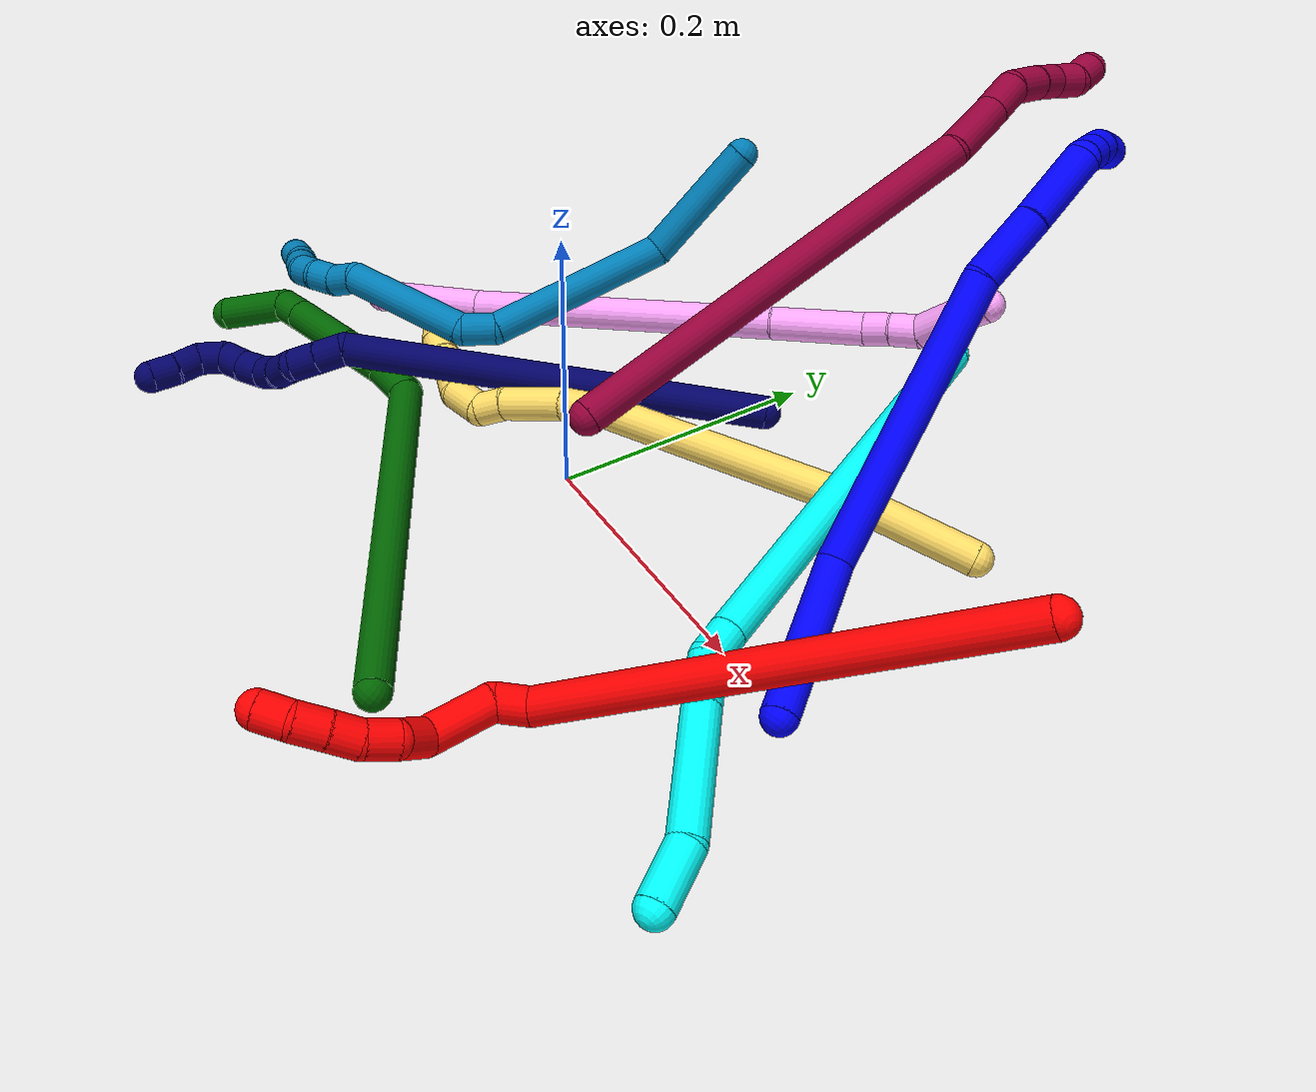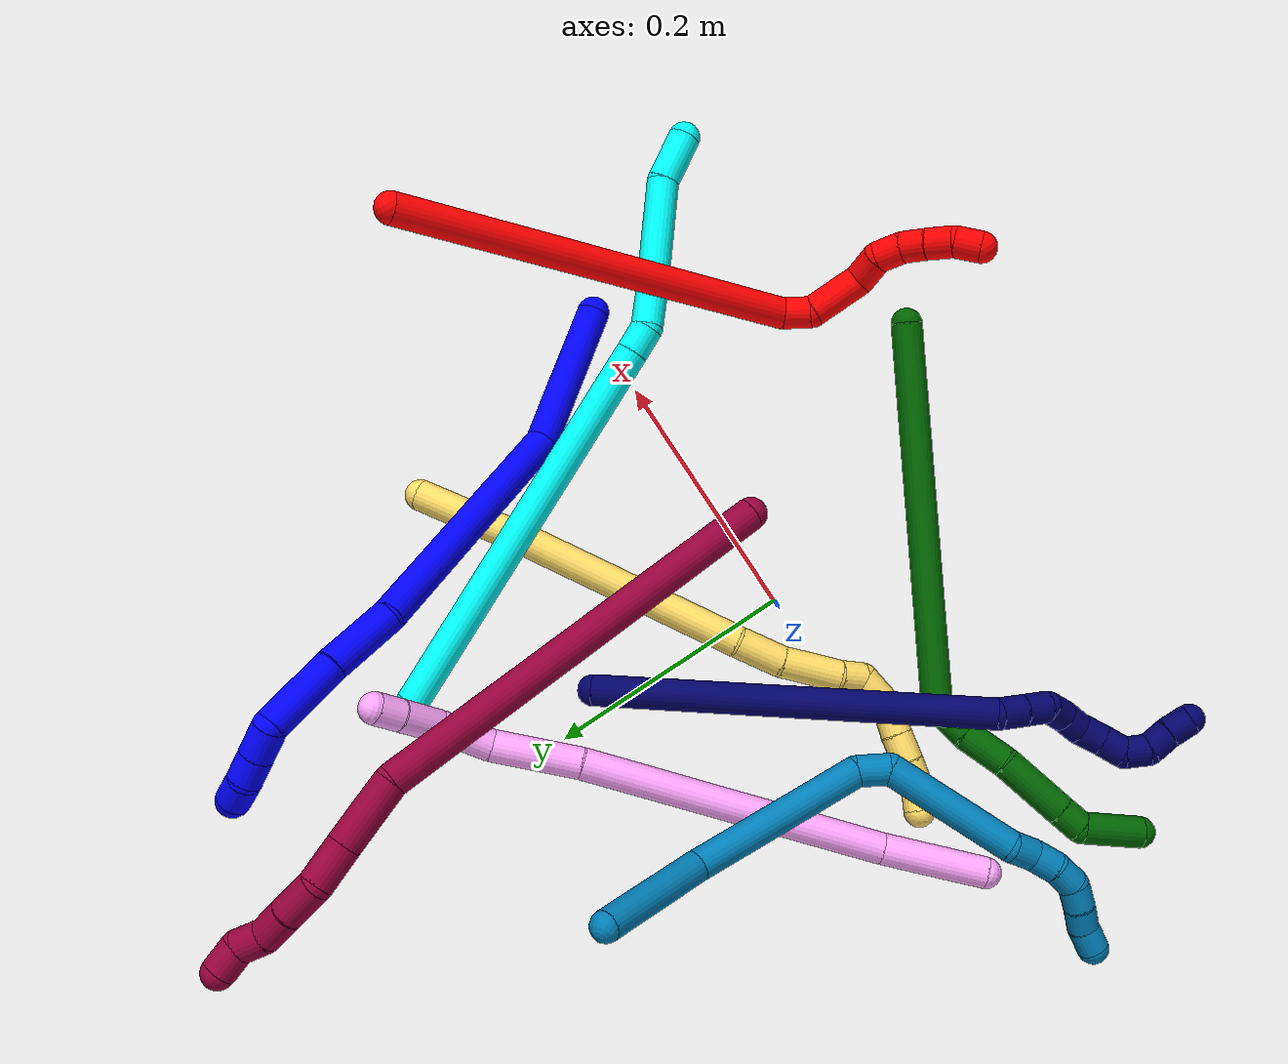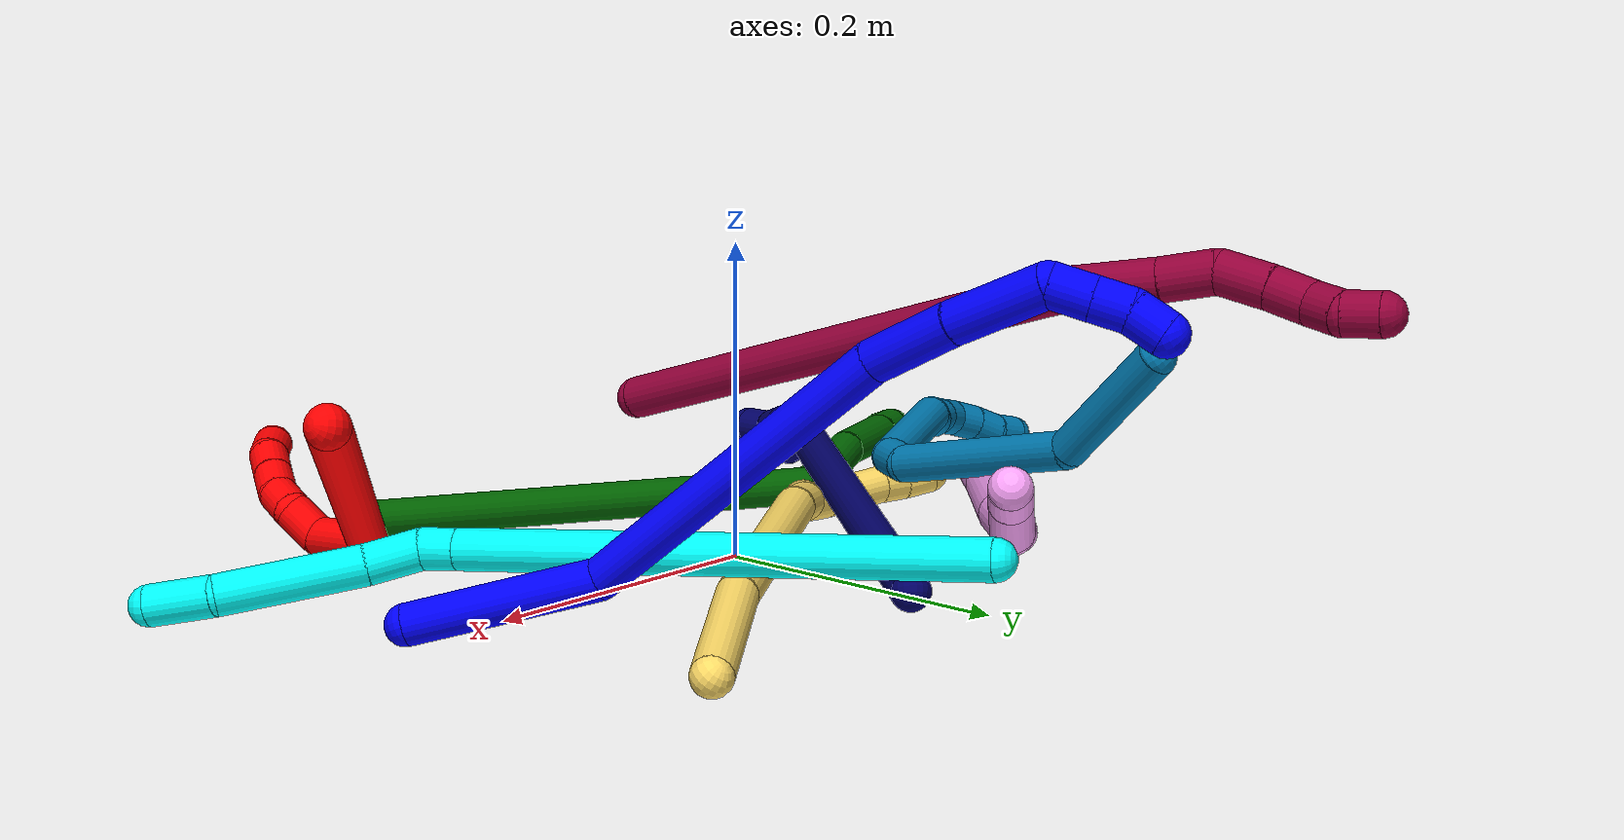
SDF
<sdf version="1.7">
 <world name="default">
  <plugin name="TubeGeneratorPlugin" filename="libtube_generator_plugin.so"/>
  <model name="photoneo_s_sensor">
   <static>1</static>
   <pose>0 0 2 1.57079 1.57079 3.14159</pose>
   <link name="link">
    <inertial><mass>0.1</mass></inertial>
    <sensor name="sensor" type="depth">
     <update_rate>30</update_rate>
     <camera>
      <horizontal_fov>1.22</horizontal_fov>
      <image><width>1920</width><height>1200</height><format>B8G8R8</format></image>
      <clip><near>0.1</near><far>4</far></clip>
      <depth_camera><output>points</output></depth_camera>
     </camera>
     <plugin name="camera_plugin" filename="libgazebo_ros_depth_camera.so">
      <baseline>0.2</baseline>
      <alwaysOn>1</alwaysOn>
      <updateRate>0.0</updateRate>
      <cameraName>camera_ir</cameraName>
      <imageTopicName>/camera/color/image_raw</imageTopicName>
      <cameraInfoTopicName>/camera/color/camera_info</cameraInfoTopicName>
      <depthImageTopicName>/camera/depth/image_raw</depthImageTopicName>
      <depthImageCameraInfoTopicName>/camera/depth/camera_info</depthImageCameraInfoTopicName>
      <pointCloudTopicName>/camera/depth/points</pointCloudTopicName>
      <frameName>fr_optical</frameName>
      <pointCloudCutoff>0.1</pointCloudCutoff>
      <pointCloudCutoffMax>2.0</pointCloudCutoffMax>
      <distortionK1>0</distortionK1>
      <distortionK2>0</distortionK2>
      <distortionK3>0</distortionK3>
      <distortionT1>0</distortionT1>
      <distortionT2>0</distortionT2>
      <CxPrime>0</CxPrime>
      <Cx>0</Cx>
      <Cy>0</Cy>
      <focalLength>0</focalLength>
      <hackBaseline>0</hackBaseline>
     </plugin>
    </sensor>
   </link>
  </model>
  <gravity>0 0 -9.8</gravity>
  <magnetic_field>6e-06 2.3e-05 -4.2e-05</magnetic_field>
  <atmosphere type="adiabatic"/>
  <physics name="default_physics" default="0" type="ode">
   <max_step_size>0.003</max_step_size>
   <real_time_factor>1</real_time_factor>
   <real_time_update_rate>1000</real_time_update_rate>
   <max_contacts>10000</max_contacts>
   <ode>
    <solver>
     <type>quick</type>
     <iters>100</iters>
     <sor>1.3</sor>
     <use_dynamic_moi_rescaling>0</use_dynamic_moi_rescaling>
    </solver>
    <constraints>
     <contact_max_correcting_vel>0</contact_max_correcting_vel>
     <contact_surface_layer>0.001</contact_surface_layer>
     <cfm>0</cfm>
     <erp>0.2</erp>
    </constraints>
   </ode>
  </physics>
  <scene><ambient>0.4 0.4 0.4 1</ambient><background>0.7 0.7 0.7 1</background><shadows>0</shadows></scene>
  <audio><device>default</device></audio>
  <spherical_coordinates>
   <surface_model>EARTH_WGS84</surface_model>
   <latitude_deg>0</latitude_deg>
   <longitude_deg>0</longitude_deg>
   <elevation>0</elevation>
   <heading_deg>0</heading_deg>
  </spherical_coordinates>
  <model name="bin">
   <static>1</static>
   <link name="bottom">
    <collision name="collision-bottom">
     <pose>0 0 -0.01 0 -0 0</pose>
     <geometry><box><size>0.8 0.6 0.02</size></box></geometry>
     <surface>
      <friction><ode><mu>100</mu><mu2>100</mu2></ode></friction>
      <contact><collide_bitmask>65535</collide_bitmask></contact>
     </surface>
    </collision>
   </link>
   <link name="west_wall">
    <collision name="collision-west_wall">
     <pose>-0.41 0 0.1 0 -0 0</pose>
     <geometry><box><size>0.02 0.6 0.2</size></box></geometry>
     <surface>
      <friction><ode><mu>100</mu><mu2>100</mu2></ode></friction>
      <contact><collide_bitmask>65535</collide_bitmask></contact>
     </surface>
    </collision>
   </link>
   <link name="east_wall">
    <collision name="collision-east_wall">
     <pose>0.41 0 0.1 0 -0 0</pose>
     <geometry><box><size>0.02 0.6 0.2</size></box></geometry>
     <surface>
      <friction><ode><mu>100</mu><mu2>100</mu2></ode></friction>
      <contact><collide_bitmask>65535</collide_bitmask></contact>
     </surface>
    </collision>
   </link>
   <link name="south_wall">
    <collision name="collision-south_wall">
     <pose>0 -0.31 0.1 0 -0 0</pose>
     <geometry><box><size>0.8 0.02 0.2</size></box></geometry>
     <surface>
      <friction><ode><mu>100</mu><mu2>100</mu2></ode></friction>
      <contact><collide_bitmask>65535</collide_bitmask></contact>
     </surface>
    </collision>
   </link>
   <link name="north_wall">
    <collision name="collision-north_wall">
     <pose>0 0.31 0.1 0 -0 0</pose>
     <geometry><box><size>0.8 0.02 0.2</size></box></geometry>
     <surface>
      <friction><ode><mu>100</mu><mu2>100</mu2></ode></friction>
      <contact><collide_bitmask>65535</collide_bitmask></contact>
     </surface>
    </collision>
   </link>
  </model>
  <model name="1">
   <static>0</static>
   <link name="1">
    <collision name="collision-cylinder-e_1_1_4">
     <pose>0.016277 -0.006592 0.05468 0.119972 0.287361 0.017378</pose>
     <geometry><cylinder><radius>0.0125</radius><length>0.114861</length></cylinder></geometry>
     <surface>
      <friction><ode><mu>1.16</mu><mu2>1.16</mu2><slip1>0</slip1><slip2>0</slip2></ode></friction>
      <contact><ode><kp>1e+06</kp><kd>1</kd><max_vel>0</max_vel><min_depth>0.001</min_depth></ode></contact>
     </surface>
    </collision>
    <visual name="visual-cylinder-e_1_1_4">
     <pose>0.016277 -0.006592 0.05468 0.119972 0.287361 0.017378</pose>
     <geometry><cylinder><radius>0.0125</radius><length>0.114861</length></cylinder></geometry>
     <material><ambient>0 0 1 1</ambient></material>
    </visual>
    <collision name="collision-cylinder-e_2_4_5">
     <pose>0.032983 0.017486 0.208892 -0.298903 0.004118 -0.00062</pose>
     <geometry><cylinder><radius>0.0125</radius><length>0.208302</length></cylinder></geometry>
     <surface>
      <friction><ode><mu>1.16</mu><mu2>1.16</mu2><slip1>0</slip1><slip2>0</slip2></ode></friction>
      <contact><ode><kp>1e+06</kp><kd>1</kd><max_vel>0</max_vel><min_depth>0.001</min_depth></ode></contact>
     </surface>
    </collision>
    <visual name="visual-cylinder-e_2_4_5">
     <pose>0.032983 0.017486 0.208892 -0.298903 0.004118 -0.00062</pose>
     <geometry><cylinder><radius>0.0125</radius><length>0.208302</length></cylinder></geometry>
     <material><ambient>0 0 1 1</ambient></material>
    </visual>
    <collision name="collision-cylinder-e_3_5_6">
     <pose>0.029452 0.050385 0.334721 -0.084577 -0.148932 0.006314</pose>
     <geometry><cylinder><radius>0.0125</radius><length>0.053375</length></cylinder></geometry>
     <surface>
      <friction><ode><mu>1.16</mu><mu2>1.16</mu2><slip1>0</slip1><slip2>0</slip2></ode></friction>
      <contact><ode><kp>1e+06</kp><kd>1</kd><max_vel>0</max_vel><min_depth>0.001</min_depth></ode></contact>
     </surface>
    </collision>
    <visual name="visual-cylinder-e_3_5_6">
     <pose>0.029452 0.050385 0.334721 -0.084577 -0.148932 0.006314</pose>
     <geometry><cylinder><radius>0.0125</radius><length>0.053375</length></cylinder></geometry>
     <material><ambient>0 0 1 1</ambient></material>
    </visual>
    <collision name="collision-cylinder-e_4_6_7">
     <pose>0.022824 0.053325 0.389964 -0.02454 -0.09191 0.001129</pose>
     <geometry><cylinder><radius>0.0125</radius><length>0.058152</length></cylinder></geometry>
     <surface>
      <friction><ode><mu>1.16</mu><mu2>1.16</mu2><slip1>0</slip1><slip2>0</slip2></ode></friction>
      <contact><ode><kp>1e+06</kp><kd>1</kd><max_vel>0</max_vel><min_depth>0.001</min_depth></ode></contact>
     </surface>
    </collision>
    <visual name="visual-cylinder-e_4_6_7">
     <pose>0.022824 0.053325 0.389964 -0.02454 -0.09191 0.001129</pose>
     <geometry><cylinder><radius>0.0125</radius><length>0.058152</length></cylinder></geometry>
     <material><ambient>0 0 1 1</ambient></material>
    </visual>
    <collision name="collision-cylinder-e_5_7_8">
     <pose>0.022077 0.046726 0.428052 0.674352 0.16277 0.057172</pose>
     <geometry><cylinder><radius>0.0125</radius><length>0.023727</length></cylinder></geometry>
     <surface>
      <friction><ode><mu>1.16</mu><mu2>1.16</mu2><slip1>0</slip1><slip2>0</slip2></ode></friction>
      <contact><ode><kp>1e+06</kp><kd>1</kd><max_vel>0</max_vel><min_depth>0.001</min_depth></ode></contact>
     </surface>
    </collision>
    <visual name="visual-cylinder-e_5_7_8">
     <pose>0.022077 0.046726 0.428052 0.674352 0.16277 0.057172</pose>
     <geometry><cylinder><radius>0.0125</radius><length>0.023727</length></cylinder></geometry>
     <material><ambient>0 0 1 1</ambient></material>
    </visual>
    <collision name="collision-cylinder-e_6_8_9">
     <pose>0.025662 0.033065 0.445136 0.67476 0.16208 0.056966</pose>
     <geometry><cylinder><radius>0.0125</radius><length>0.020605</length></cylinder></geometry>
     <surface>
      <friction><ode><mu>1.16</mu><mu2>1.16</mu2><slip1>0</slip1><slip2>0</slip2></ode></friction>
      <contact><ode><kp>1e+06</kp><kd>1</kd><max_vel>0</max_vel><min_depth>0.001</min_depth></ode></contact>
     </surface>
    </collision>
    <visual name="visual-cylinder-e_6_8_9">
     <pose>0.025662 0.033065 0.445136 0.67476 0.16208 0.056966</pose>
     <geometry><cylinder><radius>0.0125</radius><length>0.020605</length></cylinder></geometry>
     <material><ambient>0 0 1 1</ambient></material>
    </visual>
    <collision name="collision-cylinder-e_7_9_2">
     <pose>0.027826 0.018215 0.459203 0.946038 0.047813 0.024473</pose>
     <geometry><cylinder><radius>0.0125</radius><length>0.020979</length></cylinder></geometry>
     <surface>
      <friction><ode><mu>1.16</mu><mu2>1.16</mu2><slip1>0</slip1><slip2>0</slip2></ode></friction>
      <contact><ode><kp>1e+06</kp><kd>1</kd><max_vel>0</max_vel><min_depth>0.001</min_depth></ode></contact>
     </surface>
    </collision>
    <visual name="visual-cylinder-e_7_9_2">
     <pose>0.027826 0.018215 0.459203 0.946038 0.047813 0.024473</pose>
     <geometry><cylinder><radius>0.0125</radius><length>0.020979</length></cylinder></geometry>
     <material><ambient>0 0 1 1</ambient></material>
    </visual>
    <collision name="collision-sphere-2">
     <pose>0.028328 0.009717 0.465331 0 -0 0</pose>
     <geometry><sphere><radius>0.0125</radius></sphere></geometry>
     <surface>
      <friction><ode><mu>1.16</mu><mu2>1.16</mu2><slip1>0</slip1><slip2>0</slip2></ode></friction>
      <contact><ode><kp>1e+06</kp><kd>1</kd><max_vel>0</max_vel><min_depth>0.001</min_depth></ode></contact>
     </surface>
    </collision>
    <visual name="visual-sphere-2">
     <pose>0.028328 0.009717 0.465331 0 -0 0</pose>
     <geometry><sphere><radius>0.0125</radius></sphere></geometry>
     <material><ambient>0 0 1 1</ambient></material>
    </visual>
    <collision name="collision-sphere-9">
     <pose>0.027325 0.026713 0.453075 0 -0 0</pose>
     <geometry><sphere><radius>0.0125</radius></sphere></geometry>
     <surface>
      <friction><ode><mu>1.16</mu><mu2>1.16</mu2><slip1>0</slip1><slip2>0</slip2></ode></friction>
      <contact><ode><kp>1e+06</kp><kd>1</kd><max_vel>0</max_vel><min_depth>0.001</min_depth></ode></contact>
     </surface>
    </collision>
    <visual name="visual-sphere-9">
     <pose>0.027325 0.026713 0.453075 0 -0 0</pose>
     <geometry><sphere><radius>0.0125</radius></sphere></geometry>
     <material><ambient>0 0 1 1</ambient></material>
    </visual>
    <collision name="collision-sphere-4">
     <pose>0.032554 -0.013183 0.10936 0 -0 0</pose>
     <geometry><sphere><radius>0.0125</radius></sphere></geometry>
     <surface>
      <friction><ode><mu>1.16</mu><mu2>1.16</mu2><slip1>0</slip1><slip2>0</slip2></ode></friction>
      <contact><ode><kp>1e+06</kp><kd>1</kd><max_vel>0</max_vel><min_depth>0.001</min_depth></ode></contact>
     </surface>
    </collision>
    <visual name="visual-sphere-4">
     <pose>0.032554 -0.013183 0.10936 0 -0 0</pose>
     <geometry><sphere><radius>0.0125</radius></sphere></geometry>
     <material><ambient>0 0 1 1</ambient></material>
    </visual>
    <collision name="collision-sphere-1">
     <geometry><sphere><radius>0.0125</radius></sphere></geometry>
     <surface>
      <friction><ode><mu>1.16</mu><mu2>1.16</mu2><slip1>0</slip1><slip2>0</slip2></ode></friction>
      <contact><ode><kp>1e+06</kp><kd>1</kd><max_vel>0</max_vel><min_depth>0.001</min_depth></ode></contact>
     </surface>
    </collision>
    <visual name="visual-sphere-1">
     <geometry><sphere><radius>0.0125</radius></sphere></geometry>
     <material><ambient>0 0 1 1</ambient></material>
    </visual>
    <collision name="collision-sphere-8">
     <pose>0.024 0.039416 0.437196 0 -0 0</pose>
     <geometry><sphere><radius>0.0125</radius></sphere></geometry>
     <surface>
      <friction><ode><mu>1.16</mu><mu2>1.16</mu2><slip1>0</slip1><slip2>0</slip2></ode></friction>
      <contact><ode><kp>1e+06</kp><kd>1</kd><max_vel>0</max_vel><min_depth>0.001</min_depth></ode></contact>
     </surface>
    </collision>
    <visual name="visual-sphere-8">
     <pose>0.024 0.039416 0.437196 0 -0 0</pose>
     <geometry><sphere><radius>0.0125</radius></sphere></geometry>
     <material><ambient>0 0 1 1</ambient></material>
    </visual>
    <collision name="collision-sphere-5">
     <pose>0.033412 0.048155 0.308424 0 -0 0</pose>
     <geometry><sphere><radius>0.0125</radius></sphere></geometry>
     <surface>
      <friction><ode><mu>1.16</mu><mu2>1.16</mu2><slip1>0</slip1><slip2>0</slip2></ode></friction>
      <contact><ode><kp>1e+06</kp><kd>1</kd><max_vel>0</max_vel><min_depth>0.001</min_depth></ode></contact>
     </surface>
    </collision>
    <visual name="visual-sphere-5">
     <pose>0.033412 0.048155 0.308424 0 -0 0</pose>
     <geometry><sphere><radius>0.0125</radius></sphere></geometry>
     <material><ambient>0 0 1 1</ambient></material>
    </visual>
    <collision name="collision-sphere-6">
     <pose>0.025492 0.052614 0.361019 0 -0 0</pose>
     <geometry><sphere><radius>0.0125</radius></sphere></geometry>
     <surface>
      <friction><ode><mu>1.16</mu><mu2>1.16</mu2><slip1>0</slip1><slip2>0</slip2></ode></friction>
      <contact><ode><kp>1e+06</kp><kd>1</kd><max_vel>0</max_vel><min_depth>0.001</min_depth></ode></contact>
     </surface>
    </collision>
    <visual name="visual-sphere-6">
     <pose>0.025492 0.052614 0.361019 0 -0 0</pose>
     <geometry><sphere><radius>0.0125</radius></sphere></geometry>
     <material><ambient>0 0 1 1</ambient></material>
    </visual>
    <collision name="collision-sphere-7">
     <pose>0.020155 0.054035 0.418908 0 -0 0</pose>
     <geometry><sphere><radius>0.0125</radius></sphere></geometry>
     <surface>
      <friction><ode><mu>1.16</mu><mu2>1.16</mu2><slip1>0</slip1><slip2>0</slip2></ode></friction>
      <contact><ode><kp>1e+06</kp><kd>1</kd><max_vel>0</max_vel><min_depth>0.001</min_depth></ode></contact>
     </surface>
    </collision>
    <visual name="visual-sphere-7">
     <pose>0.020155 0.054035 0.418908 0 -0 0</pose>
     <geometry><sphere><radius>0.0125</radius></sphere></geometry>
     <material><ambient>0 0 1 1</ambient></material>
    </visual>
    <inertial>
     <pose>0.026551 0.021695 0.238595 0 -0 0</pose>
     <mass>0.5</mass>
     <inertia>
      <ixx>0.000929</ixx>
      <ixy>0</ixy>
      <ixz>0</ixz>
      <iyy>0.000897</iyy>
      <iyz>0</iyz>
      <izz>-0.000208</izz>
     </inertia>
    </inertial>
   </link>
   <pose>0.269686 -0.006259 0.011496 1.16408 0.038707 -2.80689</pose>
  </model>
  <model name="2">
   <static>0</static>
   <link name="2">
    <collision name="collision-cylinder-e_1_1_4">
     <pose>-0.065043 -0.096886 0.110472 0.719974 -0.416729 -0.158827</pose>
     <geometry><cylinder><radius>0.0125</radius><length>0.321382</length></cylinder></geometry>
     <surface>
      <friction><ode><mu>1.16</mu><mu2>1.16</mu2><slip1>0</slip1><slip2>0</slip2></ode></friction>
      <contact><ode><kp>1e+06</kp><kd>1</kd><max_vel>0</max_vel><min_depth>0.001</min_depth></ode></contact>
     </surface>
    </collision>
    <visual name="visual-cylinder-e_1_1_4">
     <pose>-0.065043 -0.096886 0.110472 0.719974 -0.416729 -0.158827</pose>
     <geometry><cylinder><radius>0.0125</radius><length>0.321382</length></cylinder></geometry>
     <material><ambient>1 0 0 1</ambient></material>
    </visual>
    <collision name="collision-cylinder-e_2_4_5">
     <pose>-0.128836 -0.20432 0.225887 1.13253 0.106978 0.068046</pose>
     <geometry><cylinder><radius>0.0125</radius><length>0.023429</length></cylinder></geometry>
     <surface>
      <friction><ode><mu>1.16</mu><mu2>1.16</mu2><slip1>0</slip1><slip2>0</slip2></ode></friction>
      <contact><ode><kp>1e+06</kp><kd>1</kd><max_vel>0</max_vel><min_depth>0.001</min_depth></ode></contact>
     </surface>
    </collision>
    <visual name="visual-cylinder-e_2_4_5">
     <pose>-0.128836 -0.20432 0.225887 1.13253 0.106978 0.068046</pose>
     <geometry><cylinder><radius>0.0125</radius><length>0.023429</length></cylinder></geometry>
     <material><ambient>1 0 0 1</ambient></material>
    </visual>
    <collision name="collision-cylinder-e_3_5_6">
     <pose>-0.134092 -0.236739 0.229591 1.62739 -0.288748 -0.305318</pose>
     <geometry><cylinder><radius>0.0125</radius><length>0.045707</length></cylinder></geometry>
     <surface>
      <friction><ode><mu>1.16</mu><mu2>1.16</mu2><slip1>0</slip1><slip2>0</slip2></ode></friction>
      <contact><ode><kp>1e+06</kp><kd>1</kd><max_vel>0</max_vel><min_depth>0.001</min_depth></ode></contact>
     </surface>
    </collision>
    <visual name="visual-cylinder-e_3_5_6">
     <pose>-0.134092 -0.236739 0.229591 1.62739 -0.288748 -0.305318</pose>
     <geometry><cylinder><radius>0.0125</radius><length>0.045707</length></cylinder></geometry>
     <material><ambient>1 0 0 1</ambient></material>
    </visual>
    <collision name="collision-cylinder-e_4_6_7">
     <pose>-0.136195 -0.269199 0.223416 2.00701 0.360603 0.557291</pose>
     <geometry><cylinder><radius>0.0125</radius><length>0.024969</length></cylinder></geometry>
     <surface>
      <friction><ode><mu>1.16</mu><mu2>1.16</mu2><slip1>0</slip1><slip2>0</slip2></ode></friction>
      <contact><ode><kp>1e+06</kp><kd>1</kd><max_vel>0</max_vel><min_depth>0.001</min_depth></ode></contact>
     </surface>
    </collision>
    <visual name="visual-cylinder-e_4_6_7">
     <pose>-0.136195 -0.269199 0.223416 2.00701 0.360603 0.557291</pose>
     <geometry><cylinder><radius>0.0125</radius><length>0.024969</length></cylinder></geometry>
     <material><ambient>1 0 0 1</ambient></material>
    </visual>
    <collision name="collision-cylinder-e_5_7_8">
     <pose>-0.130058 -0.290327 0.21942 1.48183 0.162219 0.148446</pose>
     <geometry><cylinder><radius>0.0125</radius><length>0.021446</length></cylinder></geometry>
     <surface>
      <friction><ode><mu>1.16</mu><mu2>1.16</mu2><slip1>0</slip1><slip2>0</slip2></ode></friction>
      <contact><ode><kp>1e+06</kp><kd>1</kd><max_vel>0</max_vel><min_depth>0.001</min_depth></ode></contact>
     </surface>
    </collision>
    <visual name="visual-cylinder-e_5_7_8">
     <pose>-0.130058 -0.290327 0.21942 1.48183 0.162219 0.148446</pose>
     <geometry><cylinder><radius>0.0125</radius><length>0.021446</length></cylinder></geometry>
     <material><ambient>1 0 0 1</ambient></material>
    </visual>
    <collision name="collision-cylinder-e_6_8_9">
     <pose>-0.124856 -0.309848 0.223286 1.25583 0.35208 0.256835</pose>
     <geometry><cylinder><radius>0.0125</radius><length>0.020124</length></cylinder></geometry>
     <surface>
      <friction><ode><mu>1.16</mu><mu2>1.16</mu2><slip1>0</slip1><slip2>0</slip2></ode></friction>
      <contact><ode><kp>1e+06</kp><kd>1</kd><max_vel>0</max_vel><min_depth>0.001</min_depth></ode></contact>
     </surface>
    </collision>
    <visual name="visual-cylinder-e_6_8_9">
     <pose>-0.124856 -0.309848 0.223286 1.25583 0.35208 0.256835</pose>
     <geometry><cylinder><radius>0.0125</radius><length>0.020124</length></cylinder></geometry>
     <material><ambient>1 0 0 1</ambient></material>
    </visual>
    <collision name="collision-cylinder-e_7_9_10">
     <pose>-0.118125 -0.3286 0.22996 1.20457 0.302116 0.208539</pose>
     <geometry><cylinder><radius>0.0125</radius><length>0.021924</length></cylinder></geometry>
     <surface>
      <friction><ode><mu>1.16</mu><mu2>1.16</mu2><slip1>0</slip1><slip2>0</slip2></ode></friction>
      <contact><ode><kp>1e+06</kp><kd>1</kd><max_vel>0</max_vel><min_depth>0.001</min_depth></ode></contact>
     </surface>
    </collision>
    <visual name="visual-cylinder-e_7_9_10">
     <pose>-0.118125 -0.3286 0.22996 1.20457 0.302116 0.208539</pose>
     <geometry><cylinder><radius>0.0125</radius><length>0.021924</length></cylinder></geometry>
     <material><ambient>1 0 0 1</ambient></material>
    </visual>
    <collision name="collision-cylinder-e_8_10_2">
     <pose>-0.113046 -0.346379 0.240266 0.884601 0.173737 0.082441</pose>
     <geometry><cylinder><radius>0.0125</radius><length>0.021017</length></cylinder></geometry>
     <surface>
      <friction><ode><mu>1.16</mu><mu2>1.16</mu2><slip1>0</slip1><slip2>0</slip2></ode></friction>
      <contact><ode><kp>1e+06</kp><kd>1</kd><max_vel>0</max_vel><min_depth>0.001</min_depth></ode></contact>
     </surface>
    </collision>
    <visual name="visual-cylinder-e_8_10_2">
     <pose>-0.113046 -0.346379 0.240266 0.884601 0.173737 0.082441</pose>
     <geometry><cylinder><radius>0.0125</radius><length>0.021017</length></cylinder></geometry>
     <material><ambient>1 0 0 1</ambient></material>
    </visual>
    <collision name="collision-sphere-2">
     <pose>-0.11123 -0.354387 0.246824 0 -0 0</pose>
     <geometry><sphere><radius>0.0125</radius></sphere></geometry>
     <surface>
      <friction><ode><mu>1.16</mu><mu2>1.16</mu2><slip1>0</slip1><slip2>0</slip2></ode></friction>
      <contact><ode><kp>1e+06</kp><kd>1</kd><max_vel>0</max_vel><min_depth>0.001</min_depth></ode></contact>
     </surface>
    </collision>
    <visual name="visual-sphere-2">
     <pose>-0.11123 -0.354387 0.246824 0 -0 0</pose>
     <geometry><sphere><radius>0.0125</radius></sphere></geometry>
     <material><ambient>1 0 0 1</ambient></material>
    </visual>
    <collision name="collision-sphere-10">
     <pose>-0.114863 -0.338371 0.233708 0 -0 0</pose>
     <geometry><sphere><radius>0.0125</radius></sphere></geometry>
     <surface>
      <friction><ode><mu>1.16</mu><mu2>1.16</mu2><slip1>0</slip1><slip2>0</slip2></ode></friction>
      <contact><ode><kp>1e+06</kp><kd>1</kd><max_vel>0</max_vel><min_depth>0.001</min_depth></ode></contact>
     </surface>
    </collision>
    <visual name="visual-sphere-10">
     <pose>-0.114863 -0.338371 0.233708 0 -0 0</pose>
     <geometry><sphere><radius>0.0125</radius></sphere></geometry>
     <material><ambient>1 0 0 1</ambient></material>
    </visual>
    <collision name="collision-sphere-9">
     <pose>-0.121386 -0.318828 0.226212 0 -0 0</pose>
     <geometry><sphere><radius>0.0125</radius></sphere></geometry>
     <surface>
      <friction><ode><mu>1.16</mu><mu2>1.16</mu2><slip1>0</slip1><slip2>0</slip2></ode></friction>
      <contact><ode><kp>1e+06</kp><kd>1</kd><max_vel>0</max_vel><min_depth>0.001</min_depth></ode></contact>
     </surface>
    </collision>
    <visual name="visual-sphere-9">
     <pose>-0.121386 -0.318828 0.226212 0 -0 0</pose>
     <geometry><sphere><radius>0.0125</radius></sphere></geometry>
     <material><ambient>1 0 0 1</ambient></material>
    </visual>
    <collision name="collision-sphere-4">
     <pose>-0.130086 -0.193773 0.220944 0 -0 0</pose>
     <geometry><sphere><radius>0.0125</radius></sphere></geometry>
     <surface>
      <friction><ode><mu>1.16</mu><mu2>1.16</mu2><slip1>0</slip1><slip2>0</slip2></ode></friction>
      <contact><ode><kp>1e+06</kp><kd>1</kd><max_vel>0</max_vel><min_depth>0.001</min_depth></ode></contact>
     </surface>
    </collision>
    <visual name="visual-sphere-4">
     <pose>-0.130086 -0.193773 0.220944 0 -0 0</pose>
     <geometry><sphere><radius>0.0125</radius></sphere></geometry>
     <material><ambient>1 0 0 1</ambient></material>
    </visual>
    <collision name="collision-sphere-1">
     <geometry><sphere><radius>0.0125</radius></sphere></geometry>
     <surface>
      <friction><ode><mu>1.16</mu><mu2>1.16</mu2><slip1>0</slip1><slip2>0</slip2></ode></friction>
      <contact><ode><kp>1e+06</kp><kd>1</kd><max_vel>0</max_vel><min_depth>0.001</min_depth></ode></contact>
     </surface>
    </collision>
    <visual name="visual-sphere-1">
     <geometry><sphere><radius>0.0125</radius></sphere></geometry>
     <material><ambient>1 0 0 1</ambient></material>
    </visual>
    <collision name="collision-sphere-8">
     <pose>-0.128326 -0.300868 0.22036 0 -0 0</pose>
     <geometry><sphere><radius>0.0125</radius></sphere></geometry>
     <surface>
      <friction><ode><mu>1.16</mu><mu2>1.16</mu2><slip1>0</slip1><slip2>0</slip2></ode></friction>
      <contact><ode><kp>1e+06</kp><kd>1</kd><max_vel>0</max_vel><min_depth>0.001</min_depth></ode></contact>
     </surface>
    </collision>
    <visual name="visual-sphere-8">
     <pose>-0.128326 -0.300868 0.22036 0 -0 0</pose>
     <geometry><sphere><radius>0.0125</radius></sphere></geometry>
     <material><ambient>1 0 0 1</ambient></material>
    </visual>
    <collision name="collision-sphere-5">
     <pose>-0.127585 -0.214867 0.23083 0 -0 0</pose>
     <geometry><sphere><radius>0.0125</radius></sphere></geometry>
     <surface>
      <friction><ode><mu>1.16</mu><mu2>1.16</mu2><slip1>0</slip1><slip2>0</slip2></ode></friction>
      <contact><ode><kp>1e+06</kp><kd>1</kd><max_vel>0</max_vel><min_depth>0.001</min_depth></ode></contact>
     </surface>
    </collision>
    <visual name="visual-sphere-5">
     <pose>-0.127585 -0.214867 0.23083 0 -0 0</pose>
     <geometry><sphere><radius>0.0125</radius></sphere></geometry>
     <material><ambient>1 0 0 1</ambient></material>
    </visual>
    <collision name="collision-sphere-6">
     <pose>-0.1406 -0.258611 0.228351 0 -0 0</pose>
     <geometry><sphere><radius>0.0125</radius></sphere></geometry>
     <surface>
      <friction><ode><mu>1.16</mu><mu2>1.16</mu2><slip1>0</slip1><slip2>0</slip2></ode></friction>
      <contact><ode><kp>1e+06</kp><kd>1</kd><max_vel>0</max_vel><min_depth>0.001</min_depth></ode></contact>
     </surface>
    </collision>
    <visual name="visual-sphere-6">
     <pose>-0.1406 -0.258611 0.228351 0 -0 0</pose>
     <geometry><sphere><radius>0.0125</radius></sphere></geometry>
     <material><ambient>1 0 0 1</ambient></material>
    </visual>
    <collision name="collision-sphere-7">
     <pose>-0.13179 -0.279787 0.21848 0 -0 0</pose>
     <geometry><sphere><radius>0.0125</radius></sphere></geometry>
     <surface>
      <friction><ode><mu>1.16</mu><mu2>1.16</mu2><slip1>0</slip1><slip2>0</slip2></ode></friction>
      <contact><ode><kp>1e+06</kp><kd>1</kd><max_vel>0</max_vel><min_depth>0.001</min_depth></ode></contact>
     </surface>
    </collision>
    <visual name="visual-sphere-7">
     <pose>-0.13179 -0.279787 0.21848 0 -0 0</pose>
     <geometry><sphere><radius>0.0125</radius></sphere></geometry>
     <material><ambient>1 0 0 1</ambient></material>
    </visual>
    <inertial>
     <pose>-0.087439 -0.160826 0.152318 0 -0 0</pose>
     <mass>0.5</mass>
     <inertia>
      <ixx>0.002117</ixx>
      <ixy>0</ixy>
      <ixz>0</ixz>
      <iyy>0.001753</iyy>
      <iyz>0</iyz>
      <izz>0.002838</izz>
     </inertia>
    </inertial>
   </link>
   <pose>0.388083 0.073624 0.156271 -2.51512 -1.24956 2.4364</pose>
  </model>
  <model name="3">
   <static>0</static>
   <link name="3">
    <collision name="collision-cylinder-e_1_1_4">
     <pose>-0.002041 -0.006985 -0.157481 3.09727 -0.012949 -0.568359</pose>
     <geometry><cylinder><radius>0.0125</radius><length>0.315298</length></cylinder></geometry>
     <surface>
      <friction><ode><mu>1.16</mu><mu2>1.16</mu2><slip1>0</slip1><slip2>0</slip2></ode></friction>
      <contact><ode><kp>1e+06</kp><kd>1</kd><max_vel>0</max_vel><min_depth>0.001</min_depth></ode></contact>
     </surface>
    </collision>
    <visual name="visual-cylinder-e_1_1_4">
     <pose>-0.002041 -0.006985 -0.157481 3.09727 -0.012949 -0.568359</pose>
     <geometry><cylinder><radius>0.0125</radius><length>0.315298</length></cylinder></geometry>
     <material><ambient>0.003922 1 0.996078 1</ambient></material>
    </visual>
    <collision name="collision-cylinder-e_2_4_5">
     <pose>-0.004102 -0.014417 -0.326227 3.10191 -0.001716 -0.086406</pose>
     <geometry><cylinder><radius>0.0125</radius><length>0.022548</length></cylinder></geometry>
     <surface>
      <friction><ode><mu>1.16</mu><mu2>1.16</mu2><slip1>0</slip1><slip2>0</slip2></ode></friction>
      <contact><ode><kp>1e+06</kp><kd>1</kd><max_vel>0</max_vel><min_depth>0.001</min_depth></ode></contact>
     </surface>
    </collision>
    <visual name="visual-cylinder-e_2_4_5">
     <pose>-0.004102 -0.014417 -0.326227 3.10191 -0.001716 -0.086406</pose>
     <geometry><cylinder><radius>0.0125</radius><length>0.022548</length></cylinder></geometry>
     <material><ambient>0.003922 1 0.996078 1</ambient></material>
    </visual>
    <collision name="collision-cylinder-e_3_5_6">
     <pose>0.001842 -0.01111 -0.352566 -2.89747 0.366511 -1.97222</pose>
     <geometry><cylinder><radius>0.0125</radius><length>0.03328</length></cylinder></geometry>
     <surface>
      <friction><ode><mu>1.16</mu><mu2>1.16</mu2><slip1>0</slip1><slip2>0</slip2></ode></friction>
      <contact><ode><kp>1e+06</kp><kd>1</kd><max_vel>0</max_vel><min_depth>0.001</min_depth></ode></contact>
     </surface>
    </collision>
    <visual name="visual-cylinder-e_3_5_6">
     <pose>0.001842 -0.01111 -0.352566 -2.89747 0.366511 -1.97222</pose>
     <geometry><cylinder><radius>0.0125</radius><length>0.03328</length></cylinder></geometry>
     <material><ambient>0.003922 1 0.996078 1</ambient></material>
    </visual>
    <collision name="collision-cylinder-e_4_6_7">
     <pose>0.025662 -0.000937 -0.407381 -2.98149 0.417501 -2.41755</pose>
     <geometry><cylinder><radius>0.0125</radius><length>0.088078</length></cylinder></geometry>
     <surface>
      <friction><ode><mu>1.16</mu><mu2>1.16</mu2><slip1>0</slip1><slip2>0</slip2></ode></friction>
      <contact><ode><kp>1e+06</kp><kd>1</kd><max_vel>0</max_vel><min_depth>0.001</min_depth></ode></contact>
     </surface>
    </collision>
    <visual name="visual-cylinder-e_4_6_7">
     <pose>0.025662 -0.000937 -0.407381 -2.98149 0.417501 -2.41755</pose>
     <geometry><cylinder><radius>0.0125</radius><length>0.088078</length></cylinder></geometry>
     <material><ambient>0.003922 1 0.996078 1</ambient></material>
    </visual>
    <collision name="collision-cylinder-e_5_7_2">
     <pose>0.045267 0.007775 -0.467316 -3.02846 0.085809 -1.29739</pose>
     <geometry><cylinder><radius>0.0125</radius><length>0.040797</length></cylinder></geometry>
     <surface>
      <friction><ode><mu>1.16</mu><mu2>1.16</mu2><slip1>0</slip1><slip2>0</slip2></ode></friction>
      <contact><ode><kp>1e+06</kp><kd>1</kd><max_vel>0</max_vel><min_depth>0.001</min_depth></ode></contact>
     </surface>
    </collision>
    <visual name="visual-cylinder-e_5_7_2">
     <pose>0.045267 0.007775 -0.467316 -3.02846 0.085809 -1.29739</pose>
     <geometry><cylinder><radius>0.0125</radius><length>0.040797</length></cylinder></geometry>
     <material><ambient>0.003922 1 0.996078 1</ambient></material>
    </visual>
    <collision name="collision-sphere-2">
     <pose>0.047015 0.01007 -0.487509 0 -0 0</pose>
     <geometry><sphere><radius>0.0125</radius></sphere></geometry>
     <surface>
      <friction><ode><mu>1.16</mu><mu2>1.16</mu2><slip1>0</slip1><slip2>0</slip2></ode></friction>
      <contact><ode><kp>1e+06</kp><kd>1</kd><max_vel>0</max_vel><min_depth>0.001</min_depth></ode></contact>
     </surface>
    </collision>
    <visual name="visual-sphere-2">
     <pose>0.047015 0.01007 -0.487509 0 -0 0</pose>
     <geometry><sphere><radius>0.0125</radius></sphere></geometry>
     <material><ambient>0.003922 1 0.996078 1</ambient></material>
    </visual>
    <collision name="collision-sphere-7">
     <pose>0.043519 0.005481 -0.447123 0 -0 0</pose>
     <geometry><sphere><radius>0.0125</radius></sphere></geometry>
     <surface>
      <friction><ode><mu>1.16</mu><mu2>1.16</mu2><slip1>0</slip1><slip2>0</slip2></ode></friction>
      <contact><ode><kp>1e+06</kp><kd>1</kd><max_vel>0</max_vel><min_depth>0.001</min_depth></ode></contact>
     </surface>
    </collision>
    <visual name="visual-sphere-7">
     <pose>0.043519 0.005481 -0.447123 0 -0 0</pose>
     <geometry><sphere><radius>0.0125</radius></sphere></geometry>
     <material><ambient>0.003922 1 0.996078 1</ambient></material>
    </visual>
    <collision name="collision-sphere-6">
     <pose>0.007805 -0.007355 -0.36764 0 -0 0</pose>
     <geometry><sphere><radius>0.0125</radius></sphere></geometry>
     <surface>
      <friction><ode><mu>1.16</mu><mu2>1.16</mu2><slip1>0</slip1><slip2>0</slip2></ode></friction>
      <contact><ode><kp>1e+06</kp><kd>1</kd><max_vel>0</max_vel><min_depth>0.001</min_depth></ode></contact>
     </surface>
    </collision>
    <visual name="visual-sphere-6">
     <pose>0.007805 -0.007355 -0.36764 0 -0 0</pose>
     <geometry><sphere><radius>0.0125</radius></sphere></geometry>
     <material><ambient>0.003922 1 0.996078 1</ambient></material>
    </visual>
    <collision name="collision-sphere-5">
     <pose>-0.004121 -0.014864 -0.337492 0 -0 0</pose>
     <geometry><sphere><radius>0.0125</radius></sphere></geometry>
     <surface>
      <friction><ode><mu>1.16</mu><mu2>1.16</mu2><slip1>0</slip1><slip2>0</slip2></ode></friction>
      <contact><ode><kp>1e+06</kp><kd>1</kd><max_vel>0</max_vel><min_depth>0.001</min_depth></ode></contact>
     </surface>
    </collision>
    <visual name="visual-sphere-5">
     <pose>-0.004121 -0.014864 -0.337492 0 -0 0</pose>
     <geometry><sphere><radius>0.0125</radius></sphere></geometry>
     <material><ambient>0.003922 1 0.996078 1</ambient></material>
    </visual>
    <collision name="collision-sphere-1">
     <geometry><sphere><radius>0.0125</radius></sphere></geometry>
     <surface>
      <friction><ode><mu>1.16</mu><mu2>1.16</mu2><slip1>0</slip1><slip2>0</slip2></ode></friction>
      <contact><ode><kp>1e+06</kp><kd>1</kd><max_vel>0</max_vel><min_depth>0.001</min_depth></ode></contact>
     </surface>
    </collision>
    <visual name="visual-sphere-1">
     <geometry><sphere><radius>0.0125</radius></sphere></geometry>
     <material><ambient>0.003922 1 0.996078 1</ambient></material>
    </visual>
    <collision name="collision-sphere-4">
     <pose>-0.004083 -0.01397 -0.314962 0 -0 0</pose>
     <geometry><sphere><radius>0.0125</radius></sphere></geometry>
     <surface>
      <friction><ode><mu>1.16</mu><mu2>1.16</mu2><slip1>0</slip1><slip2>0</slip2></ode></friction>
      <contact><ode><kp>1e+06</kp><kd>1</kd><max_vel>0</max_vel><min_depth>0.001</min_depth></ode></contact>
     </surface>
    </collision>
    <visual name="visual-sphere-4">
     <pose>-0.004083 -0.01397 -0.314962 0 -0 0</pose>
     <geometry><sphere><radius>0.0125</radius></sphere></geometry>
     <material><ambient>0.003922 1 0.996078 1</ambient></material>
    </visual>
    <inertial>
     <pose>0.006864 -0.005325 -0.247377 0 -0 0</pose>
     <mass>0.5</mass>
     <inertia>
      <ixx>0.000716</ixx>
      <ixy>0</ixy>
      <ixz>0</ixz>
      <iyy>-0.003622</iyy>
      <iyz>0</iyz>
      <izz>7.5e-05</izz>
     </inertia>
    </inertial>
   </link>
   <pose>0.089495 0.27169 0.064374 -1.46687 -0.166997 0.437774</pose>
  </model>
  <model name="4">
   <static>0</static>
   <link name="4">
    <collision name="collision-cylinder-e_1_1_4">
     <pose>-0.011271 -0.022414 0.034307 0.578705 -0.2684 -0.080345</pose>
     <geometry><cylinder><radius>0.0125</radius><length>0.085003</length></cylinder></geometry>
     <surface>
      <friction><ode><mu>1.16</mu><mu2>1.16</mu2><slip1>0</slip1><slip2>0</slip2></ode></friction>
      <contact><ode><kp>1e+06</kp><kd>1</kd><max_vel>0</max_vel><min_depth>0.001</min_depth></ode></contact>
     </surface>
    </collision>
    <visual name="visual-cylinder-e_1_1_4">
     <pose>-0.011271 -0.022414 0.034307 0.578705 -0.2684 -0.080345</pose>
     <geometry><cylinder><radius>0.0125</radius><length>0.085003</length></cylinder></geometry>
     <material><ambient>1 0.65098 0.996078 1</ambient></material>
    </visual>
    <collision name="collision-cylinder-e_2_4_5">
     <pose>-0.055911 -0.097949 0.17419 0.466176 -0.27518 -0.06572</pose>
     <geometry><cylinder><radius>0.0125</radius><length>0.245615</length></cylinder></geometry>
     <surface>
      <friction><ode><mu>1.16</mu><mu2>1.16</mu2><slip1>0</slip1><slip2>0</slip2></ode></friction>
      <contact><ode><kp>1e+06</kp><kd>1</kd><max_vel>0</max_vel><min_depth>0.001</min_depth></ode></contact>
     </surface>
    </collision>
    <visual name="visual-cylinder-e_2_4_5">
     <pose>-0.055911 -0.097949 0.17419 0.466176 -0.27518 -0.06572</pose>
     <geometry><cylinder><radius>0.0125</radius><length>0.245615</length></cylinder></geometry>
     <material><ambient>1 0.65098 0.996078 1</ambient></material>
    </visual>
    <collision name="collision-cylinder-e_3_5_6">
     <pose>-0.097319 -0.169511 0.308512 0.57034 -0.231154 -0.068042</pose>
     <geometry><cylinder><radius>0.0125</radius><length>0.070172</length></cylinder></geometry>
     <surface>
      <friction><ode><mu>1.16</mu><mu2>1.16</mu2><slip1>0</slip1><slip2>0</slip2></ode></friction>
      <contact><ode><kp>1e+06</kp><kd>1</kd><max_vel>0</max_vel><min_depth>0.001</min_depth></ode></contact>
     </surface>
    </collision>
    <visual name="visual-cylinder-e_3_5_6">
     <pose>-0.097319 -0.169511 0.308512 0.57034 -0.231154 -0.068042</pose>
     <geometry><cylinder><radius>0.0125</radius><length>0.070172</length></cylinder></geometry>
     <material><ambient>1 0.65098 0.996078 1</ambient></material>
    </visual>
    <collision name="collision-cylinder-e_4_6_7">
     <pose>-0.108418 -0.190824 0.346764 0.293572 -0.299065 -0.044542</pose>
     <geometry><cylinder><radius>0.0125</radius><length>0.020782</length></cylinder></geometry>
     <surface>
      <friction><ode><mu>1.16</mu><mu2>1.16</mu2><slip1>0</slip1><slip2>0</slip2></ode></friction>
      <contact><ode><kp>1e+06</kp><kd>1</kd><max_vel>0</max_vel><min_depth>0.001</min_depth></ode></contact>
     </surface>
    </collision>
    <visual name="visual-cylinder-e_4_6_7">
     <pose>-0.108418 -0.190824 0.346764 0.293572 -0.299065 -0.044542</pose>
     <geometry><cylinder><radius>0.0125</radius><length>0.020782</length></cylinder></geometry>
     <material><ambient>1 0.65098 0.996078 1</ambient></material>
    </visual>
    <collision name="collision-cylinder-e_5_7_8">
     <pose>-0.114892 -0.197766 0.365622 0.410346 -0.322889 -0.067758</pose>
     <geometry><cylinder><radius>0.0125</radius><length>0.02151</length></cylinder></geometry>
     <surface>
      <friction><ode><mu>1.16</mu><mu2>1.16</mu2><slip1>0</slip1><slip2>0</slip2></ode></friction>
      <contact><ode><kp>1e+06</kp><kd>1</kd><max_vel>0</max_vel><min_depth>0.001</min_depth></ode></contact>
     </surface>
    </collision>
    <visual name="visual-cylinder-e_5_7_8">
     <pose>-0.114892 -0.197766 0.365622 0.410346 -0.322889 -0.067758</pose>
     <geometry><cylinder><radius>0.0125</radius><length>0.02151</length></cylinder></geometry>
     <material><ambient>1 0.65098 0.996078 1</ambient></material>
    </visual>
    <collision name="collision-cylinder-e_6_8_9">
     <pose>-0.118901 -0.201142 0.392791 -0.038857 -0.033417 0.000649</pose>
     <geometry><cylinder><radius>0.0125</radius><length>0.035679</length></cylinder></geometry>
     <surface>
      <friction><ode><mu>1.16</mu><mu2>1.16</mu2><slip1>0</slip1><slip2>0</slip2></ode></friction>
      <contact><ode><kp>1e+06</kp><kd>1</kd><max_vel>0</max_vel><min_depth>0.001</min_depth></ode></contact>
     </surface>
    </collision>
    <visual name="visual-cylinder-e_6_8_9">
     <pose>-0.118901 -0.201142 0.392791 -0.038857 -0.033417 0.000649</pose>
     <geometry><cylinder><radius>0.0125</radius><length>0.035679</length></cylinder></geometry>
     <material><ambient>1 0.65098 0.996078 1</ambient></material>
    </visual>
    <collision name="collision-cylinder-e_7_9_2">
     <pose>-0.120315 -0.200927 0.421184 0.04513 -0.077093 -0.001741</pose>
     <geometry><cylinder><radius>0.0125</radius><length>0.021239</length></cylinder></geometry>
     <surface>
      <friction><ode><mu>1.16</mu><mu2>1.16</mu2><slip1>0</slip1><slip2>0</slip2></ode></friction>
      <contact><ode><kp>1e+06</kp><kd>1</kd><max_vel>0</max_vel><min_depth>0.001</min_depth></ode></contact>
     </surface>
    </collision>
    <visual name="visual-cylinder-e_7_9_2">
     <pose>-0.120315 -0.200927 0.421184 0.04513 -0.077093 -0.001741</pose>
     <geometry><cylinder><radius>0.0125</radius><length>0.021239</length></cylinder></geometry>
     <material><ambient>1 0.65098 0.996078 1</ambient></material>
    </visual>
    <collision name="collision-sphere-2">
     <pose>-0.121133 -0.201405 0.431761 0 -0 0</pose>
     <geometry><sphere><radius>0.0125</radius></sphere></geometry>
     <surface>
      <friction><ode><mu>1.16</mu><mu2>1.16</mu2><slip1>0</slip1><slip2>0</slip2></ode></friction>
      <contact><ode><kp>1e+06</kp><kd>1</kd><max_vel>0</max_vel><min_depth>0.001</min_depth></ode></contact>
     </surface>
    </collision>
    <visual name="visual-sphere-2">
     <pose>-0.121133 -0.201405 0.431761 0 -0 0</pose>
     <geometry><sphere><radius>0.0125</radius></sphere></geometry>
     <material><ambient>1 0.65098 0.996078 1</ambient></material>
    </visual>
    <collision name="collision-sphere-9">
     <pose>-0.119497 -0.20045 0.410607 0 -0 0</pose>
     <geometry><sphere><radius>0.0125</radius></sphere></geometry>
     <surface>
      <friction><ode><mu>1.16</mu><mu2>1.16</mu2><slip1>0</slip1><slip2>0</slip2></ode></friction>
      <contact><ode><kp>1e+06</kp><kd>1</kd><max_vel>0</max_vel><min_depth>0.001</min_depth></ode></contact>
     </surface>
    </collision>
    <visual name="visual-sphere-9">
     <pose>-0.119497 -0.20045 0.410607 0 -0 0</pose>
     <geometry><sphere><radius>0.0125</radius></sphere></geometry>
     <material><ambient>1 0.65098 0.996078 1</ambient></material>
    </visual>
    <collision name="collision-sphere-4">
     <pose>-0.022542 -0.044827 0.068614 0 -0 0</pose>
     <geometry><sphere><radius>0.0125</radius></sphere></geometry>
     <surface>
      <friction><ode><mu>1.16</mu><mu2>1.16</mu2><slip1>0</slip1><slip2>0</slip2></ode></friction>
      <contact><ode><kp>1e+06</kp><kd>1</kd><max_vel>0</max_vel><min_depth>0.001</min_depth></ode></contact>
     </surface>
    </collision>
    <visual name="visual-sphere-4">
     <pose>-0.022542 -0.044827 0.068614 0 -0 0</pose>
     <geometry><sphere><radius>0.0125</radius></sphere></geometry>
     <material><ambient>1 0.65098 0.996078 1</ambient></material>
    </visual>
    <collision name="collision-sphere-1">
     <geometry><sphere><radius>0.0125</radius></sphere></geometry>
     <surface>
      <friction><ode><mu>1.16</mu><mu2>1.16</mu2><slip1>0</slip1><slip2>0</slip2></ode></friction>
      <contact><ode><kp>1e+06</kp><kd>1</kd><max_vel>0</max_vel><min_depth>0.001</min_depth></ode></contact>
     </surface>
    </collision>
    <visual name="visual-sphere-1">
     <geometry><sphere><radius>0.0125</radius></sphere></geometry>
     <material><ambient>1 0.65098 0.996078 1</ambient></material>
    </visual>
    <collision name="collision-sphere-8">
     <pose>-0.118305 -0.201835 0.374975 0 -0 0</pose>
     <geometry><sphere><radius>0.0125</radius></sphere></geometry>
     <surface>
      <friction><ode><mu>1.16</mu><mu2>1.16</mu2><slip1>0</slip1><slip2>0</slip2></ode></friction>
      <contact><ode><kp>1e+06</kp><kd>1</kd><max_vel>0</max_vel><min_depth>0.001</min_depth></ode></contact>
     </surface>
    </collision>
    <visual name="visual-sphere-8">
     <pose>-0.118305 -0.201835 0.374975 0 -0 0</pose>
     <geometry><sphere><radius>0.0125</radius></sphere></geometry>
     <material><ambient>1 0.65098 0.996078 1</ambient></material>
    </visual>
    <collision name="collision-sphere-5">
     <pose>-0.08928 -0.151071 0.279765 0 -0 0</pose>
     <geometry><sphere><radius>0.0125</radius></sphere></geometry>
     <surface>
      <friction><ode><mu>1.16</mu><mu2>1.16</mu2><slip1>0</slip1><slip2>0</slip2></ode></friction>
      <contact><ode><kp>1e+06</kp><kd>1</kd><max_vel>0</max_vel><min_depth>0.001</min_depth></ode></contact>
     </surface>
    </collision>
    <visual name="visual-sphere-5">
     <pose>-0.08928 -0.151071 0.279765 0 -0 0</pose>
     <geometry><sphere><radius>0.0125</radius></sphere></geometry>
     <material><ambient>1 0.65098 0.996078 1</ambient></material>
    </visual>
    <collision name="collision-sphere-6">
     <pose>-0.105357 -0.18795 0.33726 0 -0 0</pose>
     <geometry><sphere><radius>0.0125</radius></sphere></geometry>
     <surface>
      <friction><ode><mu>1.16</mu><mu2>1.16</mu2><slip1>0</slip1><slip2>0</slip2></ode></friction>
      <contact><ode><kp>1e+06</kp><kd>1</kd><max_vel>0</max_vel><min_depth>0.001</min_depth></ode></contact>
     </surface>
    </collision>
    <visual name="visual-sphere-6">
     <pose>-0.105357 -0.18795 0.33726 0 -0 0</pose>
     <geometry><sphere><radius>0.0125</radius></sphere></geometry>
     <material><ambient>1 0.65098 0.996078 1</ambient></material>
    </visual>
    <collision name="collision-sphere-7">
     <pose>-0.11148 -0.193697 0.356269 0 -0 0</pose>
     <geometry><sphere><radius>0.0125</radius></sphere></geometry>
     <surface>
      <friction><ode><mu>1.16</mu><mu2>1.16</mu2><slip1>0</slip1><slip2>0</slip2></ode></friction>
      <contact><ode><kp>1e+06</kp><kd>1</kd><max_vel>0</max_vel><min_depth>0.001</min_depth></ode></contact>
     </surface>
    </collision>
    <visual name="visual-sphere-7">
     <pose>-0.11148 -0.193697 0.356269 0 -0 0</pose>
     <geometry><sphere><radius>0.0125</radius></sphere></geometry>
     <material><ambient>1 0.65098 0.996078 1</ambient></material>
    </visual>
    <inertial>
     <pose>-0.066084 -0.115043 0.210759 0 -0 0</pose>
     <mass>0.5</mass>
     <inertia>
      <ixx>0.001193</ixx>
      <ixy>0</ixy>
      <ixz>0</ixz>
      <iyy>0.001101</iyy>
      <iyz>0</iyz>
      <izz>0.000979</izz>
     </inertia>
    </inertial>
   </link>
   <pose>-0.269775 -0.020984 0.011494 0.777384 -0.451999 2.65462</pose>
  </model>
  <model name="5">
   <static>0</static>
   <link name="5">
    <collision name="collision-cylinder-e_1_1_4">
     <pose>-0.033118 -0.032678 -0.003406 1.67464 -0.789393 -0.865946</pose>
     <geometry><cylinder><radius>0.0125</radius><length>0.093301</length></cylinder></geometry>
     <surface>
      <friction><ode><mu>1.16</mu><mu2>1.16</mu2><slip1>0</slip1><slip2>0</slip2></ode></friction>
      <contact><ode><kp>1e+06</kp><kd>1</kd><max_vel>0</max_vel><min_depth>0.001</min_depth></ode></contact>
     </surface>
    </collision>
    <visual name="visual-cylinder-e_1_1_4">
     <pose>-0.033118 -0.032678 -0.003406 1.67464 -0.789393 -0.865946</pose>
     <geometry><cylinder><radius>0.0125</radius><length>0.093301</length></cylinder></geometry>
     <material><ambient>1 0.858824 0.4 1</ambient></material>
    </visual>
    <collision name="collision-cylinder-e_2_4_5">
     <pose>-0.139243 -0.119245 -0.024237 1.88355 -0.911005 -1.18508</pose>
     <geometry><cylinder><radius>0.0125</radius><length>0.184798</length></cylinder></geometry>
     <surface>
      <friction><ode><mu>1.16</mu><mu2>1.16</mu2><slip1>0</slip1><slip2>0</slip2></ode></friction>
      <contact><ode><kp>1e+06</kp><kd>1</kd><max_vel>0</max_vel><min_depth>0.001</min_depth></ode></contact>
     </surface>
    </collision>
    <visual name="visual-cylinder-e_2_4_5">
     <pose>-0.139243 -0.119245 -0.024237 1.88355 -0.911005 -1.18508</pose>
     <geometry><cylinder><radius>0.0125</radius><length>0.184798</length></cylinder></geometry>
     <material><ambient>1 0.858824 0.4 1</ambient></material>
    </visual>
    <collision name="collision-cylinder-e_3_5_6">
     <pose>-0.227405 -0.181975 -0.047998 2.19248 -0.948282 -1.56977</pose>
     <geometry><cylinder><radius>0.0125</radius><length>0.03731</length></cylinder></geometry>
     <surface>
      <friction><ode><mu>1.16</mu><mu2>1.16</mu2><slip1>0</slip1><slip2>0</slip2></ode></friction>
      <contact><ode><kp>1e+06</kp><kd>1</kd><max_vel>0</max_vel><min_depth>0.001</min_depth></ode></contact>
     </surface>
    </collision>
    <visual name="visual-cylinder-e_3_5_6">
     <pose>-0.227405 -0.181975 -0.047998 2.19248 -0.948282 -1.56977</pose>
     <geometry><cylinder><radius>0.0125</radius><length>0.03731</length></cylinder></geometry>
     <material><ambient>1 0.858824 0.4 1</ambient></material>
    </visual>
    <collision name="collision-cylinder-e_4_6_7">
     <pose>-0.259323 -0.203476 -0.065755 2.30492 -0.77689 -1.48806</pose>
     <geometry><cylinder><radius>0.0125</radius><length>0.04782</length></cylinder></geometry>
     <surface>
      <friction><ode><mu>1.16</mu><mu2>1.16</mu2><slip1>0</slip1><slip2>0</slip2></ode></friction>
      <contact><ode><kp>1e+06</kp><kd>1</kd><max_vel>0</max_vel><min_depth>0.001</min_depth></ode></contact>
     </surface>
    </collision>
    <visual name="visual-cylinder-e_4_6_7">
     <pose>-0.259323 -0.203476 -0.065755 2.30492 -0.77689 -1.48806</pose>
     <geometry><cylinder><radius>0.0125</radius><length>0.04782</length></cylinder></geometry>
     <material><ambient>1 0.858824 0.4 1</ambient></material>
    </visual>
    <collision name="collision-cylinder-e_5_7_8">
     <pose>-0.282407 -0.220496 -0.083972 2.57088 -0.664296 -1.73201</pose>
     <geometry><cylinder><radius>0.0125</radius><length>0.020508</length></cylinder></geometry>
     <surface>
      <friction><ode><mu>1.16</mu><mu2>1.16</mu2><slip1>0</slip1><slip2>0</slip2></ode></friction>
      <contact><ode><kp>1e+06</kp><kd>1</kd><max_vel>0</max_vel><min_depth>0.001</min_depth></ode></contact>
     </surface>
    </collision>
    <visual name="visual-cylinder-e_5_7_8">
     <pose>-0.282407 -0.220496 -0.083972 2.57088 -0.664296 -1.73201</pose>
     <geometry><cylinder><radius>0.0125</radius><length>0.020508</length></cylinder></geometry>
     <material><ambient>1 0.858824 0.4 1</ambient></material>
    </visual>
    <collision name="collision-cylinder-e_6_8_9">
     <pose>-0.304037 -0.228509 -0.091579 1.79008 -1.3311 -1.54984</pose>
     <geometry><cylinder><radius>0.0125</radius><length>0.031519</length></cylinder></geometry>
     <surface>
      <friction><ode><mu>1.16</mu><mu2>1.16</mu2><slip1>0</slip1><slip2>0</slip2></ode></friction>
      <contact><ode><kp>1e+06</kp><kd>1</kd><max_vel>0</max_vel><min_depth>0.001</min_depth></ode></contact>
     </surface>
    </collision>
    <visual name="visual-cylinder-e_6_8_9">
     <pose>-0.304037 -0.228509 -0.091579 1.79008 -1.3311 -1.54984</pose>
     <geometry><cylinder><radius>0.0125</radius><length>0.031519</length></cylinder></geometry>
     <material><ambient>1 0.858824 0.4 1</ambient></material>
    </visual>
    <collision name="collision-cylinder-e_7_9_10">
     <pose>-0.329519 -0.232284 -0.088375 0.030558 -1.1944 -0.020781</pose>
     <geometry><cylinder><radius>0.0125</radius><length>0.021876</length></cylinder></geometry>
     <surface>
      <friction><ode><mu>1.16</mu><mu2>1.16</mu2><slip1>0</slip1><slip2>0</slip2></ode></friction>
      <contact><ode><kp>1e+06</kp><kd>1</kd><max_vel>0</max_vel><min_depth>0.001</min_depth></ode></contact>
     </surface>
    </collision>
    <visual name="visual-cylinder-e_7_9_10">
     <pose>-0.329519 -0.232284 -0.088375 0.030558 -1.1944 -0.020781</pose>
     <geometry><cylinder><radius>0.0125</radius><length>0.021876</length></cylinder></geometry>
     <material><ambient>1 0.858824 0.4 1</ambient></material>
    </visual>
    <collision name="collision-cylinder-e_8_10_11">
     <pose>-0.350342 -0.233129 -0.081173 0.223115 -1.27344 -0.165294</pose>
     <geometry><cylinder><radius>0.0125</radius><length>0.022278</length></cylinder></geometry>
     <surface>
      <friction><ode><mu>1.16</mu><mu2>1.16</mu2><slip1>0</slip1><slip2>0</slip2></ode></friction>
      <contact><ode><kp>1e+06</kp><kd>1</kd><max_vel>0</max_vel><min_depth>0.001</min_depth></ode></contact>
     </surface>
    </collision>
    <visual name="visual-cylinder-e_8_10_11">
     <pose>-0.350342 -0.233129 -0.081173 0.223115 -1.27344 -0.165294</pose>
     <geometry><cylinder><radius>0.0125</radius><length>0.022278</length></cylinder></geometry>
     <material><ambient>1 0.858824 0.4 1</ambient></material>
    </visual>
    <collision name="collision-cylinder-e_9_11_12">
     <pose>-0.37072 -0.233884 -0.075431 0.012826 -1.31353 -0.009888</pose>
     <geometry><cylinder><radius>0.0125</radius><length>0.020119</length></cylinder></geometry>
     <surface>
      <friction><ode><mu>1.16</mu><mu2>1.16</mu2><slip1>0</slip1><slip2>0</slip2></ode></friction>
      <contact><ode><kp>1e+06</kp><kd>1</kd><max_vel>0</max_vel><min_depth>0.001</min_depth></ode></contact>
     </surface>
    </collision>
    <visual name="visual-cylinder-e_9_11_12">
     <pose>-0.37072 -0.233884 -0.075431 0.012826 -1.31353 -0.009888</pose>
     <geometry><cylinder><radius>0.0125</radius><length>0.020119</length></cylinder></geometry>
     <material><ambient>1 0.858824 0.4 1</ambient></material>
    </visual>
    <collision name="collision-cylinder-e_10_12_2">
     <pose>-0.389202 -0.232829 -0.06768 -0.206552 -1.02598 0.116632</pose>
     <geometry><cylinder><radius>0.0125</radius><length>0.020471</length></cylinder></geometry>
     <surface>
      <friction><ode><mu>1.16</mu><mu2>1.16</mu2><slip1>0</slip1><slip2>0</slip2></ode></friction>
      <contact><ode><kp>1e+06</kp><kd>1</kd><max_vel>0</max_vel><min_depth>0.001</min_depth></ode></contact>
     </surface>
    </collision>
    <visual name="visual-cylinder-e_10_12_2">
     <pose>-0.389202 -0.232829 -0.06768 -0.206552 -1.02598 0.116632</pose>
     <geometry><cylinder><radius>0.0125</radius><length>0.020471</length></cylinder></geometry>
     <material><ambient>1 0.858824 0.4 1</ambient></material>
    </visual>
    <collision name="collision-sphere-2">
     <pose>-0.397956 -0.231741 -0.062488 0 -0 0</pose>
     <geometry><sphere><radius>0.0125</radius></sphere></geometry>
     <surface>
      <friction><ode><mu>1.16</mu><mu2>1.16</mu2><slip1>0</slip1><slip2>0</slip2></ode></friction>
      <contact><ode><kp>1e+06</kp><kd>1</kd><max_vel>0</max_vel><min_depth>0.001</min_depth></ode></contact>
     </surface>
    </collision>
    <visual name="visual-sphere-2">
     <pose>-0.397956 -0.231741 -0.062488 0 -0 0</pose>
     <geometry><sphere><radius>0.0125</radius></sphere></geometry>
     <material><ambient>1 0.858824 0.4 1</ambient></material>
    </visual>
    <collision name="collision-sphere-12">
     <pose>-0.380449 -0.233916 -0.072872 0 -0 0</pose>
     <geometry><sphere><radius>0.0125</radius></sphere></geometry>
     <surface>
      <friction><ode><mu>1.16</mu><mu2>1.16</mu2><slip1>0</slip1><slip2>0</slip2></ode></friction>
      <contact><ode><kp>1e+06</kp><kd>1</kd><max_vel>0</max_vel><min_depth>0.001</min_depth></ode></contact>
     </surface>
    </collision>
    <visual name="visual-sphere-12">
     <pose>-0.380449 -0.233916 -0.072872 0 -0 0</pose>
     <geometry><sphere><radius>0.0125</radius></sphere></geometry>
     <material><ambient>1 0.858824 0.4 1</ambient></material>
    </visual>
    <collision name="collision-sphere-11">
     <pose>-0.360992 -0.233851 -0.07799 0 -0 0</pose>
     <geometry><sphere><radius>0.0125</radius></sphere></geometry>
     <surface>
      <friction><ode><mu>1.16</mu><mu2>1.16</mu2><slip1>0</slip1><slip2>0</slip2></ode></friction>
      <contact><ode><kp>1e+06</kp><kd>1</kd><max_vel>0</max_vel><min_depth>0.001</min_depth></ode></contact>
     </surface>
    </collision>
    <visual name="visual-sphere-11">
     <pose>-0.360992 -0.233851 -0.07799 0 -0 0</pose>
     <geometry><sphere><radius>0.0125</radius></sphere></geometry>
     <material><ambient>1 0.858824 0.4 1</ambient></material>
    </visual>
    <collision name="collision-sphere-10">
     <pose>-0.339691 -0.232407 -0.084356 0 -0 0</pose>
     <geometry><sphere><radius>0.0125</radius></sphere></geometry>
     <surface>
      <friction><ode><mu>1.16</mu><mu2>1.16</mu2><slip1>0</slip1><slip2>0</slip2></ode></friction>
      <contact><ode><kp>1e+06</kp><kd>1</kd><max_vel>0</max_vel><min_depth>0.001</min_depth></ode></contact>
     </surface>
    </collision>
    <visual name="visual-sphere-10">
     <pose>-0.339691 -0.232407 -0.084356 0 -0 0</pose>
     <geometry><sphere><radius>0.0125</radius></sphere></geometry>
     <material><ambient>1 0.858824 0.4 1</ambient></material>
    </visual>
    <collision name="collision-sphere-9">
     <pose>-0.319347 -0.232161 -0.092393 0 -0 0</pose>
     <geometry><sphere><radius>0.0125</radius></sphere></geometry>
     <surface>
      <friction><ode><mu>1.16</mu><mu2>1.16</mu2><slip1>0</slip1><slip2>0</slip2></ode></friction>
      <contact><ode><kp>1e+06</kp><kd>1</kd><max_vel>0</max_vel><min_depth>0.001</min_depth></ode></contact>
     </surface>
    </collision>
    <visual name="visual-sphere-9">
     <pose>-0.319347 -0.232161 -0.092393 0 -0 0</pose>
     <geometry><sphere><radius>0.0125</radius></sphere></geometry>
     <material><ambient>1 0.858824 0.4 1</ambient></material>
    </visual>
    <collision name="collision-sphere-4">
     <pose>-0.066237 -0.065356 -0.006811 0 -0 0</pose>
     <geometry><sphere><radius>0.0125</radius></sphere></geometry>
     <surface>
      <friction><ode><mu>1.16</mu><mu2>1.16</mu2><slip1>0</slip1><slip2>0</slip2></ode></friction>
      <contact><ode><kp>1e+06</kp><kd>1</kd><max_vel>0</max_vel><min_depth>0.001</min_depth></ode></contact>
     </surface>
    </collision>
    <visual name="visual-sphere-4">
     <pose>-0.066237 -0.065356 -0.006811 0 -0 0</pose>
     <geometry><sphere><radius>0.0125</radius></sphere></geometry>
     <material><ambient>1 0.858824 0.4 1</ambient></material>
    </visual>
    <collision name="collision-sphere-1">
     <geometry><sphere><radius>0.0125</radius></sphere></geometry>
     <surface>
      <friction><ode><mu>1.16</mu><mu2>1.16</mu2><slip1>0</slip1><slip2>0</slip2></ode></friction>
      <contact><ode><kp>1e+06</kp><kd>1</kd><max_vel>0</max_vel><min_depth>0.001</min_depth></ode></contact>
     </surface>
    </collision>
    <visual name="visual-sphere-1">
     <geometry><sphere><radius>0.0125</radius></sphere></geometry>
     <material><ambient>1 0.858824 0.4 1</ambient></material>
    </visual>
    <collision name="collision-sphere-8">
     <pose>-0.288728 -0.224857 -0.090766 0 -0 0</pose>
     <geometry><sphere><radius>0.0125</radius></sphere></geometry>
     <surface>
      <friction><ode><mu>1.16</mu><mu2>1.16</mu2><slip1>0</slip1><slip2>0</slip2></ode></friction>
      <contact><ode><kp>1e+06</kp><kd>1</kd><max_vel>0</max_vel><min_depth>0.001</min_depth></ode></contact>
     </surface>
    </collision>
    <visual name="visual-sphere-8">
     <pose>-0.288728 -0.224857 -0.090766 0 -0 0</pose>
     <geometry><sphere><radius>0.0125</radius></sphere></geometry>
     <material><ambient>1 0.858824 0.4 1</ambient></material>
    </visual>
    <collision name="collision-sphere-5">
     <pose>-0.21225 -0.173133 -0.041663 0 -0 0</pose>
     <geometry><sphere><radius>0.0125</radius></sphere></geometry>
     <surface>
      <friction><ode><mu>1.16</mu><mu2>1.16</mu2><slip1>0</slip1><slip2>0</slip2></ode></friction>
      <contact><ode><kp>1e+06</kp><kd>1</kd><max_vel>0</max_vel><min_depth>0.001</min_depth></ode></contact>
     </surface>
    </collision>
    <visual name="visual-sphere-5">
     <pose>-0.21225 -0.173133 -0.041663 0 -0 0</pose>
     <geometry><sphere><radius>0.0125</radius></sphere></geometry>
     <material><ambient>1 0.858824 0.4 1</ambient></material>
    </visual>
    <collision name="collision-sphere-6">
     <pose>-0.242561 -0.190818 -0.054333 0 -0 0</pose>
     <geometry><sphere><radius>0.0125</radius></sphere></geometry>
     <surface>
      <friction><ode><mu>1.16</mu><mu2>1.16</mu2><slip1>0</slip1><slip2>0</slip2></ode></friction>
      <contact><ode><kp>1e+06</kp><kd>1</kd><max_vel>0</max_vel><min_depth>0.001</min_depth></ode></contact>
     </surface>
    </collision>
    <visual name="visual-sphere-6">
     <pose>-0.242561 -0.190818 -0.054333 0 -0 0</pose>
     <geometry><sphere><radius>0.0125</radius></sphere></geometry>
     <material><ambient>1 0.858824 0.4 1</ambient></material>
    </visual>
    <collision name="collision-sphere-7">
     <pose>-0.276085 -0.216134 -0.077178 0 -0 0</pose>
     <geometry><sphere><radius>0.0125</radius></sphere></geometry>
     <surface>
      <friction><ode><mu>1.16</mu><mu2>1.16</mu2><slip1>0</slip1><slip2>0</slip2></ode></friction>
      <contact><ode><kp>1e+06</kp><kd>1</kd><max_vel>0</max_vel><min_depth>0.001</min_depth></ode></contact>
     </surface>
    </collision>
    <visual name="visual-sphere-7">
     <pose>-0.276085 -0.216134 -0.077178 0 -0 0</pose>
     <geometry><sphere><radius>0.0125</radius></sphere></geometry>
     <material><ambient>1 0.858824 0.4 1</ambient></material>
    </visual>
    <inertial>
     <pose>-0.191042 -0.146152 -0.041971 0 -0 0</pose>
     <mass>0.5</mass>
     <inertia>
      <ixx>-0.000227</ixx>
      <ixy>0</ixy>
      <ixz>0</ixz>
      <iyy>-9e-06</iyy>
      <iyz>0</iyz>
      <izz>0.000861</izz>
     </inertia>
    </inertial>
   </link>
   <pose>0.224022 0.187035 0.011494 -0.63977 -0.19924 -0.077136</pose>
  </model>
  <model name="6">
   <static>0</static>
   <link name="6">
    <collision name="collision-cylinder-e_1_1_4">
     <pose>-0.126014 0.061031 -0.057641 -2.32763 -0.983135 1.78593</pose>
     <geometry><cylinder><radius>0.0125</radius><length>0.302832</length></cylinder></geometry>
     <surface>
      <friction><ode><mu>1.16</mu><mu2>1.16</mu2><slip1>0</slip1><slip2>0</slip2></ode></friction>
      <contact><ode><kp>1e+06</kp><kd>1</kd><max_vel>0</max_vel><min_depth>0.001</min_depth></ode></contact>
     </surface>
    </collision>
    <visual name="visual-cylinder-e_1_1_4">
     <pose>-0.126014 0.061031 -0.057641 -2.32763 -0.983135 1.78593</pose>
     <geometry><cylinder><radius>0.0125</radius><length>0.302832</length></cylinder></geometry>
     <material><ambient>0 0.392157 0.003922 1</ambient></material>
    </visual>
    <collision name="collision-cylinder-e_2_4_5">
     <pose>-0.259667 0.135775 -0.114987 -1.54933 -0.508095 0.497748</pose>
     <geometry><cylinder><radius>0.0125</radius><length>0.0314</length></cylinder></geometry>
     <surface>
      <friction><ode><mu>1.16</mu><mu2>1.16</mu2><slip1>0</slip1><slip2>0</slip2></ode></friction>
      <contact><ode><kp>1e+06</kp><kd>1</kd><max_vel>0</max_vel><min_depth>0.001</min_depth></ode></contact>
     </surface>
    </collision>
    <visual name="visual-cylinder-e_2_4_5">
     <pose>-0.259667 0.135775 -0.114987 -1.54933 -0.508095 0.497748</pose>
     <geometry><cylinder><radius>0.0125</radius><length>0.0314</length></cylinder></geometry>
     <material><ambient>0 0.392157 0.003922 1</ambient></material>
    </visual>
    <collision name="collision-cylinder-e_3_5_6">
     <pose>-0.27428 0.166636 -0.111917 -1.41035 -0.38182 0.32608</pose>
     <geometry><cylinder><radius>0.0125</radius><length>0.037437</length></cylinder></geometry>
     <surface>
      <friction><ode><mu>1.16</mu><mu2>1.16</mu2><slip1>0</slip1><slip2>0</slip2></ode></friction>
      <contact><ode><kp>1e+06</kp><kd>1</kd><max_vel>0</max_vel><min_depth>0.001</min_depth></ode></contact>
     </surface>
    </collision>
    <visual name="visual-cylinder-e_3_5_6">
     <pose>-0.27428 0.166636 -0.111917 -1.41035 -0.38182 0.32608</pose>
     <geometry><cylinder><radius>0.0125</radius><length>0.037437</length></cylinder></geometry>
     <material><ambient>0 0.392157 0.003922 1</ambient></material>
    </visual>
    <collision name="collision-cylinder-e_4_6_7">
     <pose>-0.29648 0.207119 -0.104257 -1.36443 -0.568318 0.465889</pose>
     <geometry><cylinder><radius>0.0125</radius><length>0.056577</length></cylinder></geometry>
     <surface>
      <friction><ode><mu>1.16</mu><mu2>1.16</mu2><slip1>0</slip1><slip2>0</slip2></ode></friction>
      <contact><ode><kp>1e+06</kp><kd>1</kd><max_vel>0</max_vel><min_depth>0.001</min_depth></ode></contact>
     </surface>
    </collision>
    <visual name="visual-cylinder-e_4_6_7">
     <pose>-0.29648 0.207119 -0.104257 -1.36443 -0.568318 0.465889</pose>
     <geometry><cylinder><radius>0.0125</radius><length>0.056577</length></cylinder></geometry>
     <material><ambient>0 0.392157 0.003922 1</ambient></material>
    </visual>
    <collision name="collision-cylinder-e_5_7_8">
     <pose>-0.317335 0.239012 -0.097365 -1.34051 -0.569667 0.456106</pose>
     <geometry><cylinder><radius>0.0125</radius><length>0.020875</length></cylinder></geometry>
     <surface>
      <friction><ode><mu>1.16</mu><mu2>1.16</mu2><slip1>0</slip1><slip2>0</slip2></ode></friction>
      <contact><ode><kp>1e+06</kp><kd>1</kd><max_vel>0</max_vel><min_depth>0.001</min_depth></ode></contact>
     </surface>
    </collision>
    <visual name="visual-cylinder-e_5_7_8">
     <pose>-0.317335 0.239012 -0.097365 -1.34051 -0.569667 0.456106</pose>
     <geometry><cylinder><radius>0.0125</radius><length>0.020875</length></cylinder></geometry>
     <material><ambient>0 0.392157 0.003922 1</ambient></material>
    </visual>
    <collision name="collision-cylinder-e_6_8_2">
     <pose>-0.328953 0.264098 -0.076972 -0.732227 -0.237654 0.091484</pose>
     <geometry><cylinder><radius>0.0125</radius><length>0.05088</length></cylinder></geometry>
     <surface>
      <friction><ode><mu>1.16</mu><mu2>1.16</mu2><slip1>0</slip1><slip2>0</slip2></ode></friction>
      <contact><ode><kp>1e+06</kp><kd>1</kd><max_vel>0</max_vel><min_depth>0.001</min_depth></ode></contact>
     </surface>
    </collision>
    <visual name="visual-cylinder-e_6_8_2">
     <pose>-0.328953 0.264098 -0.076972 -0.732227 -0.237654 0.091484</pose>
     <geometry><cylinder><radius>0.0125</radius><length>0.05088</length></cylinder></geometry>
     <material><ambient>0 0.392157 0.003922 1</ambient></material>
    </visual>
    <collision name="collision-sphere-2">
     <pose>-0.334942 0.280627 -0.058584 0 -0 0</pose>
     <geometry><sphere><radius>0.0125</radius></sphere></geometry>
     <surface>
      <friction><ode><mu>1.16</mu><mu2>1.16</mu2><slip1>0</slip1><slip2>0</slip2></ode></friction>
      <contact><ode><kp>1e+06</kp><kd>1</kd><max_vel>0</max_vel><min_depth>0.001</min_depth></ode></contact>
     </surface>
    </collision>
    <visual name="visual-sphere-2">
     <pose>-0.334942 0.280627 -0.058584 0 -0 0</pose>
     <geometry><sphere><radius>0.0125</radius></sphere></geometry>
     <material><ambient>0 0.392157 0.003922 1</ambient></material>
    </visual>
    <collision name="collision-sphere-4">
     <pose>-0.252029 0.122061 -0.115281 0 -0 0</pose>
     <geometry><sphere><radius>0.0125</radius></sphere></geometry>
     <surface>
      <friction><ode><mu>1.16</mu><mu2>1.16</mu2><slip1>0</slip1><slip2>0</slip2></ode></friction>
      <contact><ode><kp>1e+06</kp><kd>1</kd><max_vel>0</max_vel><min_depth>0.001</min_depth></ode></contact>
     </surface>
    </collision>
    <visual name="visual-sphere-4">
     <pose>-0.252029 0.122061 -0.115281 0 -0 0</pose>
     <geometry><sphere><radius>0.0125</radius></sphere></geometry>
     <material><ambient>0 0.392157 0.003922 1</ambient></material>
    </visual>
    <collision name="collision-sphere-1">
     <geometry><sphere><radius>0.0125</radius></sphere></geometry>
     <surface>
      <friction><ode><mu>1.16</mu><mu2>1.16</mu2><slip1>0</slip1><slip2>0</slip2></ode></friction>
      <contact><ode><kp>1e+06</kp><kd>1</kd><max_vel>0</max_vel><min_depth>0.001</min_depth></ode></contact>
     </surface>
    </collision>
    <visual name="visual-sphere-1">
     <geometry><sphere><radius>0.0125</radius></sphere></geometry>
     <material><ambient>0 0.392157 0.003922 1</ambient></material>
    </visual>
    <collision name="collision-sphere-8">
     <pose>-0.322964 0.247569 -0.095359 0 -0 0</pose>
     <geometry><sphere><radius>0.0125</radius></sphere></geometry>
     <surface>
      <friction><ode><mu>1.16</mu><mu2>1.16</mu2><slip1>0</slip1><slip2>0</slip2></ode></friction>
      <contact><ode><kp>1e+06</kp><kd>1</kd><max_vel>0</max_vel><min_depth>0.001</min_depth></ode></contact>
     </surface>
    </collision>
    <visual name="visual-sphere-8">
     <pose>-0.322964 0.247569 -0.095359 0 -0 0</pose>
     <geometry><sphere><radius>0.0125</radius></sphere></geometry>
     <material><ambient>0 0.392157 0.003922 1</ambient></material>
    </visual>
    <collision name="collision-sphere-5">
     <pose>-0.267305 0.149488 -0.114692 0 -0 0</pose>
     <geometry><sphere><radius>0.0125</radius></sphere></geometry>
     <surface>
      <friction><ode><mu>1.16</mu><mu2>1.16</mu2><slip1>0</slip1><slip2>0</slip2></ode></friction>
      <contact><ode><kp>1e+06</kp><kd>1</kd><max_vel>0</max_vel><min_depth>0.001</min_depth></ode></contact>
     </surface>
    </collision>
    <visual name="visual-sphere-5">
     <pose>-0.267305 0.149488 -0.114692 0 -0 0</pose>
     <geometry><sphere><radius>0.0125</radius></sphere></geometry>
     <material><ambient>0 0.392157 0.003922 1</ambient></material>
    </visual>
    <collision name="collision-sphere-6">
     <pose>-0.281255 0.183784 -0.109142 0 -0 0</pose>
     <geometry><sphere><radius>0.0125</radius></sphere></geometry>
     <surface>
      <friction><ode><mu>1.16</mu><mu2>1.16</mu2><slip1>0</slip1><slip2>0</slip2></ode></friction>
      <contact><ode><kp>1e+06</kp><kd>1</kd><max_vel>0</max_vel><min_depth>0.001</min_depth></ode></contact>
     </surface>
    </collision>
    <visual name="visual-sphere-6">
     <pose>-0.281255 0.183784 -0.109142 0 -0 0</pose>
     <geometry><sphere><radius>0.0125</radius></sphere></geometry>
     <material><ambient>0 0.392157 0.003922 1</ambient></material>
    </visual>
    <collision name="collision-sphere-7">
     <pose>-0.311705 0.230455 -0.099371 0 -0 0</pose>
     <geometry><sphere><radius>0.0125</radius></sphere></geometry>
     <surface>
      <friction><ode><mu>1.16</mu><mu2>1.16</mu2><slip1>0</slip1><slip2>0</slip2></ode></friction>
      <contact><ode><kp>1e+06</kp><kd>1</kd><max_vel>0</max_vel><min_depth>0.001</min_depth></ode></contact>
     </surface>
    </collision>
    <visual name="visual-sphere-7">
     <pose>-0.311705 0.230455 -0.099371 0 -0 0</pose>
     <geometry><sphere><radius>0.0125</radius></sphere></geometry>
     <material><ambient>0 0.392157 0.003922 1</ambient></material>
    </visual>
    <inertial>
     <pose>-0.193436 0.118257 -0.074206 0 -0 0</pose>
     <mass>0.5</mass>
     <inertia>
      <ixx>0.001005</ixx>
      <ixy>0</ixy>
      <ixz>0</ixz>
      <iyy>0.00303</iyy>
      <iyz>0</iyz>
      <izz>0.000978</izz>
     </inertia>
    </inertial>
   </link>
   <pose>0.125688 -0.2082 0.011703 2.47154 -0.581097 -0.585772</pose>
  </model>
  <model name="7">
   <static>0</static>
   <link name="7">
    <collision name="collision-cylinder-e_1_1_4">
     <pose>-0.044557 -0.116475 0.097897 0.871847 -0.284877 -0.133405</pose>
     <geometry><cylinder><radius>0.0125</radius><length>0.317084</length></cylinder></geometry>
     <surface>
      <friction><ode><mu>1.16</mu><mu2>1.16</mu2><slip1>0</slip1><slip2>0</slip2></ode></friction>
      <contact><ode><kp>1e+06</kp><kd>1</kd><max_vel>0</max_vel><min_depth>0.001</min_depth></ode></contact>
     </surface>
    </collision>
    <visual name="visual-cylinder-e_1_1_4">
     <pose>-0.044557 -0.116475 0.097897 0.871847 -0.284877 -0.133405</pose>
     <geometry><cylinder><radius>0.0125</radius><length>0.317084</length></cylinder></geometry>
     <material><ambient>0.003922 0 0.403922 1</ambient></material>
    </visual>
    <collision name="collision-cylinder-e_2_4_5">
     <pose>-0.091563 -0.24339 0.19805 1.35791 -0.225455 -0.182196</pose>
     <geometry><cylinder><radius>0.0125</radius><length>0.021916</length></cylinder></geometry>
     <surface>
      <friction><ode><mu>1.16</mu><mu2>1.16</mu2><slip1>0</slip1><slip2>0</slip2></ode></friction>
      <contact><ode><kp>1e+06</kp><kd>1</kd><max_vel>0</max_vel><min_depth>0.001</min_depth></ode></contact>
     </surface>
    </collision>
    <visual name="visual-cylinder-e_2_4_5">
     <pose>-0.091563 -0.24339 0.19805 1.35791 -0.225455 -0.182196</pose>
     <geometry><cylinder><radius>0.0125</radius><length>0.021916</length></cylinder></geometry>
     <material><ambient>0.003922 0 0.403922 1</ambient></material>
    </visual>
    <collision name="collision-cylinder-e_3_5_6">
     <pose>-0.096333 -0.263729 0.202453 1.3573 -0.22518 -0.181862</pose>
     <geometry><cylinder><radius>0.0125</radius><length>0.020784</length></cylinder></geometry>
     <surface>
      <friction><ode><mu>1.16</mu><mu2>1.16</mu2><slip1>0</slip1><slip2>0</slip2></ode></friction>
      <contact><ode><kp>1e+06</kp><kd>1</kd><max_vel>0</max_vel><min_depth>0.001</min_depth></ode></contact>
     </surface>
    </collision>
    <visual name="visual-cylinder-e_3_5_6">
     <pose>-0.096333 -0.263729 0.202453 1.3573 -0.22518 -0.181862</pose>
     <geometry><cylinder><radius>0.0125</radius><length>0.020784</length></cylinder></geometry>
     <material><ambient>0.003922 0 0.403922 1</ambient></material>
    </visual>
    <collision name="collision-cylinder-e_4_6_7">
     <pose>-0.105362 -0.280921 0.203109 1.77231 -0.733603 -0.879715</pose>
     <geometry><cylinder><radius>0.0125</radius><length>0.020041</length></cylinder></geometry>
     <surface>
      <friction><ode><mu>1.16</mu><mu2>1.16</mu2><slip1>0</slip1><slip2>0</slip2></ode></friction>
      <contact><ode><kp>1e+06</kp><kd>1</kd><max_vel>0</max_vel><min_depth>0.001</min_depth></ode></contact>
     </surface>
    </collision>
    <visual name="visual-cylinder-e_4_6_7">
     <pose>-0.105362 -0.280921 0.203109 1.77231 -0.733603 -0.879715</pose>
     <geometry><cylinder><radius>0.0125</radius><length>0.020041</length></cylinder></geometry>
     <material><ambient>0.003922 0 0.403922 1</ambient></material>
    </visual>
    <collision name="collision-cylinder-e_5_7_8">
     <pose>-0.120018 -0.294279 0.201858 1.53152 -0.91842 -0.887574</pose>
     <geometry><cylinder><radius>0.0125</radius><length>0.020001</length></cylinder></geometry>
     <surface>
      <friction><ode><mu>1.16</mu><mu2>1.16</mu2><slip1>0</slip1><slip2>0</slip2></ode></friction>
      <contact><ode><kp>1e+06</kp><kd>1</kd><max_vel>0</max_vel><min_depth>0.001</min_depth></ode></contact>
     </surface>
    </collision>
    <visual name="visual-cylinder-e_5_7_8">
     <pose>-0.120018 -0.294279 0.201858 1.53152 -0.91842 -0.887574</pose>
     <geometry><cylinder><radius>0.0125</radius><length>0.020001</length></cylinder></geometry>
     <material><ambient>0.003922 0 0.403922 1</ambient></material>
    </visual>
    <collision name="collision-cylinder-e_6_8_9">
     <pose>-0.134769 -0.306407 0.20642 0.951193 -0.740437 -0.394578</pose>
     <geometry><cylinder><radius>0.0125</radius><length>0.020172</length></cylinder></geometry>
     <surface>
      <friction><ode><mu>1.16</mu><mu2>1.16</mu2><slip1>0</slip1><slip2>0</slip2></ode></friction>
      <contact><ode><kp>1e+06</kp><kd>1</kd><max_vel>0</max_vel><min_depth>0.001</min_depth></ode></contact>
     </surface>
    </collision>
    <visual name="visual-cylinder-e_6_8_9">
     <pose>-0.134769 -0.306407 0.20642 0.951193 -0.740437 -0.394578</pose>
     <geometry><cylinder><radius>0.0125</radius><length>0.020172</length></cylinder></geometry>
     <material><ambient>0.003922 0 0.403922 1</ambient></material>
    </visual>
    <collision name="collision-cylinder-e_7_9_10">
     <pose>-0.148447 -0.317669 0.215814 0.798084 -0.757811 -0.332664</pose>
     <geometry><cylinder><radius>0.0125</radius><length>0.020002</length></cylinder></geometry>
     <surface>
      <friction><ode><mu>1.16</mu><mu2>1.16</mu2><slip1>0</slip1><slip2>0</slip2></ode></friction>
      <contact><ode><kp>1e+06</kp><kd>1</kd><max_vel>0</max_vel><min_depth>0.001</min_depth></ode></contact>
     </surface>
    </collision>
    <visual name="visual-cylinder-e_7_9_10">
     <pose>-0.148447 -0.317669 0.215814 0.798084 -0.757811 -0.332664</pose>
     <geometry><cylinder><radius>0.0125</radius><length>0.020002</length></cylinder></geometry>
     <material><ambient>0.003922 0 0.403922 1</ambient></material>
    </visual>
    <collision name="collision-cylinder-e_8_10_11">
     <pose>-0.156885 -0.331432 0.22581 1.04882 -0.157039 -0.090961</pose>
     <geometry><cylinder><radius>0.0125</radius><length>0.02</length></cylinder></geometry>
     <surface>
      <friction><ode><mu>1.16</mu><mu2>1.16</mu2><slip1>0</slip1><slip2>0</slip2></ode></friction>
      <contact><ode><kp>1e+06</kp><kd>1</kd><max_vel>0</max_vel><min_depth>0.001</min_depth></ode></contact>
     </surface>
    </collision>
    <visual name="visual-cylinder-e_8_10_11">
     <pose>-0.156885 -0.331432 0.22581 1.04882 -0.157039 -0.090961</pose>
     <geometry><cylinder><radius>0.0125</radius><length>0.02</length></cylinder></geometry>
     <material><ambient>0.003922 0 0.403922 1</ambient></material>
    </visual>
    <collision name="collision-cylinder-e_9_11_12">
     <pose>-0.154497 -0.348575 0.234014 1.20571 0.406263 0.28168</pose>
     <geometry><cylinder><radius>0.0125</radius><length>0.020001</length></cylinder></geometry>
     <surface>
      <friction><ode><mu>1.16</mu><mu2>1.16</mu2><slip1>0</slip1><slip2>0</slip2></ode></friction>
      <contact><ode><kp>1e+06</kp><kd>1</kd><max_vel>0</max_vel><min_depth>0.001</min_depth></ode></contact>
     </surface>
    </collision>
    <visual name="visual-cylinder-e_9_11_12">
     <pose>-0.154497 -0.348575 0.234014 1.20571 0.406263 0.28168</pose>
     <geometry><cylinder><radius>0.0125</radius><length>0.020001</length></cylinder></geometry>
     <material><ambient>0.003922 0 0.403922 1</ambient></material>
    </visual>
    <collision name="collision-cylinder-e_10_12_2">
     <pose>-0.147719 -0.36586 0.241327 1.13693 0.286515 0.18377</pose>
     <geometry><cylinder><radius>0.0125</radius><length>0.02</length></cylinder></geometry>
     <surface>
      <friction><ode><mu>1.16</mu><mu2>1.16</mu2><slip1>0</slip1><slip2>0</slip2></ode></friction>
      <contact><ode><kp>1e+06</kp><kd>1</kd><max_vel>0</max_vel><min_depth>0.001</min_depth></ode></contact>
     </surface>
    </collision>
    <visual name="visual-cylinder-e_10_12_2">
     <pose>-0.147719 -0.36586 0.241327 1.13693 0.286515 0.18377</pose>
     <geometry><cylinder><radius>0.0125</radius><length>0.02</length></cylinder></geometry>
     <material><ambient>0.003922 0 0.403922 1</ambient></material>
    </visual>
    <collision name="collision-sphere-2">
     <pose>-0.144893 -0.374563 0.245359 0 -0 0</pose>
     <geometry><sphere><radius>0.0125</radius></sphere></geometry>
     <surface>
      <friction><ode><mu>1.16</mu><mu2>1.16</mu2><slip1>0</slip1><slip2>0</slip2></ode></friction>
      <contact><ode><kp>1e+06</kp><kd>1</kd><max_vel>0</max_vel><min_depth>0.001</min_depth></ode></contact>
     </surface>
    </collision>
    <visual name="visual-sphere-2">
     <pose>-0.144893 -0.374563 0.245359 0 -0 0</pose>
     <geometry><sphere><radius>0.0125</radius></sphere></geometry>
     <material><ambient>0.003922 0 0.403922 1</ambient></material>
    </visual>
    <collision name="collision-sphere-12">
     <pose>-0.150545 -0.357156 0.237294 0 -0 0</pose>
     <geometry><sphere><radius>0.0125</radius></sphere></geometry>
     <surface>
      <friction><ode><mu>1.16</mu><mu2>1.16</mu2><slip1>0</slip1><slip2>0</slip2></ode></friction>
      <contact><ode><kp>1e+06</kp><kd>1</kd><max_vel>0</max_vel><min_depth>0.001</min_depth></ode></contact>
     </surface>
    </collision>
    <visual name="visual-sphere-12">
     <pose>-0.150545 -0.357156 0.237294 0 -0 0</pose>
     <geometry><sphere><radius>0.0125</radius></sphere></geometry>
     <material><ambient>0.003922 0 0.403922 1</ambient></material>
    </visual>
    <collision name="collision-sphere-11">
     <pose>-0.158449 -0.339994 0.230735 0 -0 0</pose>
     <geometry><sphere><radius>0.0125</radius></sphere></geometry>
     <surface>
      <friction><ode><mu>1.16</mu><mu2>1.16</mu2><slip1>0</slip1><slip2>0</slip2></ode></friction>
      <contact><ode><kp>1e+06</kp><kd>1</kd><max_vel>0</max_vel><min_depth>0.001</min_depth></ode></contact>
     </surface>
    </collision>
    <visual name="visual-sphere-11">
     <pose>-0.158449 -0.339994 0.230735 0 -0 0</pose>
     <geometry><sphere><radius>0.0125</radius></sphere></geometry>
     <material><ambient>0.003922 0 0.403922 1</ambient></material>
    </visual>
    <collision name="collision-sphere-10">
     <pose>-0.155321 -0.32287 0.220885 0 -0 0</pose>
     <geometry><sphere><radius>0.0125</radius></sphere></geometry>
     <surface>
      <friction><ode><mu>1.16</mu><mu2>1.16</mu2><slip1>0</slip1><slip2>0</slip2></ode></friction>
      <contact><ode><kp>1e+06</kp><kd>1</kd><max_vel>0</max_vel><min_depth>0.001</min_depth></ode></contact>
     </surface>
    </collision>
    <visual name="visual-sphere-10">
     <pose>-0.155321 -0.32287 0.220885 0 -0 0</pose>
     <geometry><sphere><radius>0.0125</radius></sphere></geometry>
     <material><ambient>0.003922 0 0.403922 1</ambient></material>
    </visual>
    <collision name="collision-sphere-9">
     <pose>-0.141573 -0.312468 0.210743 0 -0 0</pose>
     <geometry><sphere><radius>0.0125</radius></sphere></geometry>
     <surface>
      <friction><ode><mu>1.16</mu><mu2>1.16</mu2><slip1>0</slip1><slip2>0</slip2></ode></friction>
      <contact><ode><kp>1e+06</kp><kd>1</kd><max_vel>0</max_vel><min_depth>0.001</min_depth></ode></contact>
     </surface>
    </collision>
    <visual name="visual-sphere-9">
     <pose>-0.141573 -0.312468 0.210743 0 -0 0</pose>
     <geometry><sphere><radius>0.0125</radius></sphere></geometry>
     <material><ambient>0.003922 0 0.403922 1</ambient></material>
    </visual>
    <collision name="collision-sphere-4">
     <pose>-0.089113 -0.232951 0.195793 0 -0 0</pose>
     <geometry><sphere><radius>0.0125</radius></sphere></geometry>
     <surface>
      <friction><ode><mu>1.16</mu><mu2>1.16</mu2><slip1>0</slip1><slip2>0</slip2></ode></friction>
      <contact><ode><kp>1e+06</kp><kd>1</kd><max_vel>0</max_vel><min_depth>0.001</min_depth></ode></contact>
     </surface>
    </collision>
    <visual name="visual-sphere-4">
     <pose>-0.089113 -0.232951 0.195793 0 -0 0</pose>
     <geometry><sphere><radius>0.0125</radius></sphere></geometry>
     <material><ambient>0.003922 0 0.403922 1</ambient></material>
    </visual>
    <collision name="collision-sphere-1">
     <geometry><sphere><radius>0.0125</radius></sphere></geometry>
     <surface>
      <friction><ode><mu>1.16</mu><mu2>1.16</mu2><slip1>0</slip1><slip2>0</slip2></ode></friction>
      <contact><ode><kp>1e+06</kp><kd>1</kd><max_vel>0</max_vel><min_depth>0.001</min_depth></ode></contact>
     </surface>
    </collision>
    <visual name="visual-sphere-1">
     <geometry><sphere><radius>0.0125</radius></sphere></geometry>
     <material><ambient>0.003922 0 0.403922 1</ambient></material>
    </visual>
    <collision name="collision-sphere-8">
     <pose>-0.127965 -0.300346 0.202096 0 -0 0</pose>
     <geometry><sphere><radius>0.0125</radius></sphere></geometry>
     <surface>
      <friction><ode><mu>1.16</mu><mu2>1.16</mu2><slip1>0</slip1><slip2>0</slip2></ode></friction>
      <contact><ode><kp>1e+06</kp><kd>1</kd><max_vel>0</max_vel><min_depth>0.001</min_depth></ode></contact>
     </surface>
    </collision>
    <visual name="visual-sphere-8">
     <pose>-0.127965 -0.300346 0.202096 0 -0 0</pose>
     <geometry><sphere><radius>0.0125</radius></sphere></geometry>
     <material><ambient>0.003922 0 0.403922 1</ambient></material>
    </visual>
    <collision name="collision-sphere-5">
     <pose>-0.094012 -0.253829 0.200307 0 -0 0</pose>
     <geometry><sphere><radius>0.0125</radius></sphere></geometry>
     <surface>
      <friction><ode><mu>1.16</mu><mu2>1.16</mu2><slip1>0</slip1><slip2>0</slip2></ode></friction>
      <contact><ode><kp>1e+06</kp><kd>1</kd><max_vel>0</max_vel><min_depth>0.001</min_depth></ode></contact>
     </surface>
    </collision>
    <visual name="visual-sphere-5">
     <pose>-0.094012 -0.253829 0.200307 0 -0 0</pose>
     <geometry><sphere><radius>0.0125</radius></sphere></geometry>
     <material><ambient>0.003922 0 0.403922 1</ambient></material>
    </visual>
    <collision name="collision-sphere-6">
     <pose>-0.098653 -0.273628 0.204599 0 -0 0</pose>
     <geometry><sphere><radius>0.0125</radius></sphere></geometry>
     <surface>
      <friction><ode><mu>1.16</mu><mu2>1.16</mu2><slip1>0</slip1><slip2>0</slip2></ode></friction>
      <contact><ode><kp>1e+06</kp><kd>1</kd><max_vel>0</max_vel><min_depth>0.001</min_depth></ode></contact>
     </surface>
    </collision>
    <visual name="visual-sphere-6">
     <pose>-0.098653 -0.273628 0.204599 0 -0 0</pose>
     <geometry><sphere><radius>0.0125</radius></sphere></geometry>
     <material><ambient>0.003922 0 0.403922 1</ambient></material>
    </visual>
    <collision name="collision-sphere-7">
     <pose>-0.112072 -0.288213 0.20162 0 -0 0</pose>
     <geometry><sphere><radius>0.0125</radius></sphere></geometry>
     <surface>
      <friction><ode><mu>1.16</mu><mu2>1.16</mu2><slip1>0</slip1><slip2>0</slip2></ode></friction>
      <contact><ode><kp>1e+06</kp><kd>1</kd><max_vel>0</max_vel><min_depth>0.001</min_depth></ode></contact>
     </surface>
    </collision>
    <visual name="visual-sphere-7">
     <pose>-0.112072 -0.288213 0.20162 0 -0 0</pose>
     <geometry><sphere><radius>0.0125</radius></sphere></geometry>
     <material><ambient>0.003922 0 0.403922 1</ambient></material>
    </visual>
    <inertial>
     <pose>-0.075038 -0.185432 0.140403 0 -0 0</pose>
     <mass>0.5</mass>
     <inertia>
      <ixx>0.002195</ixx>
      <ixy>0</ixy>
      <ixz>0</ixz>
      <iyy>0.001413</iyy>
      <iyz>0</iyz>
      <izz>0.002745</izz>
     </inertia>
    </inertial>
   </link>
   <pose>0.020568 0.158088 0.011498 0.508639 -0.212074 -0.312207</pose>
  </model>
  <model name="8">
   <static>0</static>
   <link name="8">
    <collision name="collision-cylinder-e_1_1_4">
     <pose>0.010494 0.014892 0.159375 -0.093167 0.065462 -0.003053</pose>
     <geometry><cylinder><radius>0.0125</radius><length>0.320826</length></cylinder></geometry>
     <surface>
      <friction><ode><mu>1.16</mu><mu2>1.16</mu2><slip1>0</slip1><slip2>0</slip2></ode></friction>
      <contact><ode><kp>1e+06</kp><kd>1</kd><max_vel>0</max_vel><min_depth>0.001</min_depth></ode></contact>
     </surface>
    </collision>
    <visual name="visual-cylinder-e_1_1_4">
     <pose>0.010494 0.014892 0.159375 -0.093167 0.065462 -0.003053</pose>
     <geometry><cylinder><radius>0.0125</radius><length>0.320826</length></cylinder></geometry>
     <material><ambient>0.584314 0 0.227451 1</ambient></material>
    </visual>
    <collision name="collision-cylinder-e_2_4_5">
     <pose>0.023475 0.023525 0.344043 0.242585 0.095188 0.011611</pose>
     <geometry><cylinder><radius>0.0125</radius><length>0.052346</length></cylinder></geometry>
     <surface>
      <friction><ode><mu>1.16</mu><mu2>1.16</mu2><slip1>0</slip1><slip2>0</slip2></ode></friction>
      <contact><ode><kp>1e+06</kp><kd>1</kd><max_vel>0</max_vel><min_depth>0.001</min_depth></ode></contact>
     </surface>
    </collision>
    <visual name="visual-cylinder-e_2_4_5">
     <pose>0.023475 0.023525 0.344043 0.242585 0.095188 0.011611</pose>
     <geometry><cylinder><radius>0.0125</radius><length>0.052346</length></cylinder></geometry>
     <material><ambient>0.584314 0 0.227451 1</ambient></material>
    </visual>
    <collision name="collision-cylinder-e_3_5_6">
     <pose>0.028175 0.013628 0.384551 0.234678 0.140466 0.016585</pose>
     <geometry><cylinder><radius>0.0125</radius><length>0.031603</length></cylinder></geometry>
     <surface>
      <friction><ode><mu>1.16</mu><mu2>1.16</mu2><slip1>0</slip1><slip2>0</slip2></ode></friction>
      <contact><ode><kp>1e+06</kp><kd>1</kd><max_vel>0</max_vel><min_depth>0.001</min_depth></ode></contact>
     </surface>
    </collision>
    <visual name="visual-cylinder-e_3_5_6">
     <pose>0.028175 0.013628 0.384551 0.234678 0.140466 0.016585</pose>
     <geometry><cylinder><radius>0.0125</radius><length>0.031603</length></cylinder></geometry>
     <material><ambient>0.584314 0 0.227451 1</ambient></material>
    </visual>
    <collision name="collision-cylinder-e_4_6_7">
     <pose>0.025906 0.005697 0.413492 0.303176 -0.302095 -0.046494</pose>
     <geometry><cylinder><radius>0.0125</radius><length>0.030123</length></cylinder></geometry>
     <surface>
      <friction><ode><mu>1.16</mu><mu2>1.16</mu2><slip1>0</slip1><slip2>0</slip2></ode></friction>
      <contact><ode><kp>1e+06</kp><kd>1</kd><max_vel>0</max_vel><min_depth>0.001</min_depth></ode></contact>
     </surface>
    </collision>
    <visual name="visual-cylinder-e_4_6_7">
     <pose>0.025906 0.005697 0.413492 0.303176 -0.302095 -0.046494</pose>
     <geometry><cylinder><radius>0.0125</radius><length>0.030123</length></cylinder></geometry>
     <material><ambient>0.584314 0 0.227451 1</ambient></material>
    </visual>
    <collision name="collision-cylinder-e_5_7_8">
     <pose>0.01731 -0.002314 0.437645 0.342389 -0.35578 -0.062147</pose>
     <geometry><cylinder><radius>0.0125</radius><length>0.023622</length></cylinder></geometry>
     <surface>
      <friction><ode><mu>1.16</mu><mu2>1.16</mu2><slip1>0</slip1><slip2>0</slip2></ode></friction>
      <contact><ode><kp>1e+06</kp><kd>1</kd><max_vel>0</max_vel><min_depth>0.001</min_depth></ode></contact>
     </surface>
    </collision>
    <visual name="visual-cylinder-e_5_7_8">
     <pose>0.01731 -0.002314 0.437645 0.342389 -0.35578 -0.062147</pose>
     <geometry><cylinder><radius>0.0125</radius><length>0.023622</length></cylinder></geometry>
     <material><ambient>0.584314 0 0.227451 1</ambient></material>
    </visual>
    <collision name="collision-cylinder-e_6_8_9">
     <pose>0.008889 -0.005275 0.457444 -0.080418 -0.429628 0.017555</pose>
     <geometry><cylinder><radius>0.0125</radius><length>0.020681</length></cylinder></geometry>
     <surface>
      <friction><ode><mu>1.16</mu><mu2>1.16</mu2><slip1>0</slip1><slip2>0</slip2></ode></friction>
      <contact><ode><kp>1e+06</kp><kd>1</kd><max_vel>0</max_vel><min_depth>0.001</min_depth></ode></contact>
     </surface>
    </collision>
    <visual name="visual-cylinder-e_6_8_9">
     <pose>0.008889 -0.005275 0.457444 -0.080418 -0.429628 0.017555</pose>
     <geometry><cylinder><radius>0.0125</radius><length>0.020681</length></cylinder></geometry>
     <material><ambient>0.584314 0 0.227451 1</ambient></material>
    </visual>
    <collision name="collision-cylinder-e_7_9_2">
     <pose>0.004458 -0.007302 0.476834 0.270778 -0.01189 -0.00162</pose>
     <geometry><cylinder><radius>0.0125</radius><length>0.020798</length></cylinder></geometry>
     <surface>
      <friction><ode><mu>1.16</mu><mu2>1.16</mu2><slip1>0</slip1><slip2>0</slip2></ode></friction>
      <contact><ode><kp>1e+06</kp><kd>1</kd><max_vel>0</max_vel><min_depth>0.001</min_depth></ode></contact>
     </surface>
    </collision>
    <visual name="visual-cylinder-e_7_9_2">
     <pose>0.004458 -0.007302 0.476834 0.270778 -0.01189 -0.00162</pose>
     <geometry><cylinder><radius>0.0125</radius><length>0.020798</length></cylinder></geometry>
     <material><ambient>0.584314 0 0.227451 1</ambient></material>
    </visual>
    <collision name="collision-sphere-2">
     <pose>0.004335 -0.010083 0.486853 0 -0 0</pose>
     <geometry><sphere><radius>0.0125</radius></sphere></geometry>
     <surface>
      <friction><ode><mu>1.16</mu><mu2>1.16</mu2><slip1>0</slip1><slip2>0</slip2></ode></friction>
      <contact><ode><kp>1e+06</kp><kd>1</kd><max_vel>0</max_vel><min_depth>0.001</min_depth></ode></contact>
     </surface>
    </collision>
    <visual name="visual-sphere-2">
     <pose>0.004335 -0.010083 0.486853 0 -0 0</pose>
     <geometry><sphere><radius>0.0125</radius></sphere></geometry>
     <material><ambient>0.584314 0 0.227451 1</ambient></material>
    </visual>
    <collision name="collision-sphere-9">
     <pose>0.004582 -0.00452 0.466814 0 -0 0</pose>
     <geometry><sphere><radius>0.0125</radius></sphere></geometry>
     <surface>
      <friction><ode><mu>1.16</mu><mu2>1.16</mu2><slip1>0</slip1><slip2>0</slip2></ode></friction>
      <contact><ode><kp>1e+06</kp><kd>1</kd><max_vel>0</max_vel><min_depth>0.001</min_depth></ode></contact>
     </surface>
    </collision>
    <visual name="visual-sphere-9">
     <pose>0.004582 -0.00452 0.466814 0 -0 0</pose>
     <geometry><sphere><radius>0.0125</radius></sphere></geometry>
     <material><ambient>0.584314 0 0.227451 1</ambient></material>
    </visual>
    <collision name="collision-sphere-4">
     <pose>0.020987 0.029783 0.318751 0 -0 0</pose>
     <geometry><sphere><radius>0.0125</radius></sphere></geometry>
     <surface>
      <friction><ode><mu>1.16</mu><mu2>1.16</mu2><slip1>0</slip1><slip2>0</slip2></ode></friction>
      <contact><ode><kp>1e+06</kp><kd>1</kd><max_vel>0</max_vel><min_depth>0.001</min_depth></ode></contact>
     </surface>
    </collision>
    <visual name="visual-sphere-4">
     <pose>0.020987 0.029783 0.318751 0 -0 0</pose>
     <geometry><sphere><radius>0.0125</radius></sphere></geometry>
     <material><ambient>0.584314 0 0.227451 1</ambient></material>
    </visual>
    <collision name="collision-sphere-1">
     <geometry><sphere><radius>0.0125</radius></sphere></geometry>
     <surface>
      <friction><ode><mu>1.16</mu><mu2>1.16</mu2><slip1>0</slip1><slip2>0</slip2></ode></friction>
      <contact><ode><kp>1e+06</kp><kd>1</kd><max_vel>0</max_vel><min_depth>0.001</min_depth></ode></contact>
     </surface>
    </collision>
    <visual name="visual-sphere-1">
     <geometry><sphere><radius>0.0125</radius></sphere></geometry>
     <material><ambient>0.584314 0 0.227451 1</ambient></material>
    </visual>
    <collision name="collision-sphere-8">
     <pose>0.013196 -0.006031 0.448073 0 -0 0</pose>
     <geometry><sphere><radius>0.0125</radius></sphere></geometry>
     <surface>
      <friction><ode><mu>1.16</mu><mu2>1.16</mu2><slip1>0</slip1><slip2>0</slip2></ode></friction>
      <contact><ode><kp>1e+06</kp><kd>1</kd><max_vel>0</max_vel><min_depth>0.001</min_depth></ode></contact>
     </surface>
    </collision>
    <visual name="visual-sphere-8">
     <pose>0.013196 -0.006031 0.448073 0 -0 0</pose>
     <geometry><sphere><radius>0.0125</radius></sphere></geometry>
     <material><ambient>0.584314 0 0.227451 1</ambient></material>
    </visual>
    <collision name="collision-sphere-5">
     <pose>0.025962 0.017266 0.369334 0 -0 0</pose>
     <geometry><sphere><radius>0.0125</radius></sphere></geometry>
     <surface>
      <friction><ode><mu>1.16</mu><mu2>1.16</mu2><slip1>0</slip1><slip2>0</slip2></ode></friction>
      <contact><ode><kp>1e+06</kp><kd>1</kd><max_vel>0</max_vel><min_depth>0.001</min_depth></ode></contact>
     </surface>
    </collision>
    <visual name="visual-sphere-5">
     <pose>0.025962 0.017266 0.369334 0 -0 0</pose>
     <geometry><sphere><radius>0.0125</radius></sphere></geometry>
     <material><ambient>0.584314 0 0.227451 1</ambient></material>
    </visual>
    <collision name="collision-sphere-6">
     <pose>0.030387 0.00999 0.399768 0 -0 0</pose>
     <geometry><sphere><radius>0.0125</radius></sphere></geometry>
     <surface>
      <friction><ode><mu>1.16</mu><mu2>1.16</mu2><slip1>0</slip1><slip2>0</slip2></ode></friction>
      <contact><ode><kp>1e+06</kp><kd>1</kd><max_vel>0</max_vel><min_depth>0.001</min_depth></ode></contact>
     </surface>
    </collision>
    <visual name="visual-sphere-6">
     <pose>0.030387 0.00999 0.399768 0 -0 0</pose>
     <geometry><sphere><radius>0.0125</radius></sphere></geometry>
     <material><ambient>0.584314 0 0.227451 1</ambient></material>
    </visual>
    <collision name="collision-sphere-7">
     <pose>0.021425 0.001404 0.427216 0 -0 0</pose>
     <geometry><sphere><radius>0.0125</radius></sphere></geometry>
     <surface>
      <friction><ode><mu>1.16</mu><mu2>1.16</mu2><slip1>0</slip1><slip2>0</slip2></ode></friction>
      <contact><ode><kp>1e+06</kp><kd>1</kd><max_vel>0</max_vel><min_depth>0.001</min_depth></ode></contact>
     </surface>
    </collision>
    <visual name="visual-sphere-7">
     <pose>0.021425 0.001404 0.427216 0 -0 0</pose>
     <geometry><sphere><radius>0.0125</radius></sphere></geometry>
     <material><ambient>0.584314 0 0.227451 1</ambient></material>
    </visual>
    <inertial>
     <pose>0.013903 0.012591 0.246931 0 -0 0</pose>
     <mass>0.5</mass>
     <inertia>
      <ixx>0.002776</ixx>
      <ixy>0</ixy>
      <ixz>0</ixz>
      <iyy>0.002769</iyy>
      <iyz>0</iyz>
      <izz>-0.000393</izz>
     </inertia>
    </inertial>
   </link>
   <pose>0.066474 -0.020695 0.110033 1.18316 -0.986764 -2.70634</pose>
  </model>
  <model name="9">
   <static>0</static>
   <link name="9">
    <collision name="collision-cylinder-e_1_1_4">
     <pose>-0.005546 -0.023243 -0.043371 2.64963 -0.112224 -0.440216</pose>
     <geometry><cylinder><radius>0.0125</radius><length>0.099037</length></cylinder></geometry>
     <surface>
      <friction><ode><mu>1.16</mu><mu2>1.16</mu2><slip1>0</slip1><slip2>0</slip2></ode></friction>
      <contact><ode><kp>1e+06</kp><kd>1</kd><max_vel>0</max_vel><min_depth>0.001</min_depth></ode></contact>
     </surface>
    </collision>
    <visual name="visual-cylinder-e_1_1_4">
     <pose>-0.005546 -0.023243 -0.043371 2.64963 -0.112224 -0.440216</pose>
     <geometry><cylinder><radius>0.0125</radius><length>0.099037</length></cylinder></geometry>
     <material><ambient>0 0.490196 0.709804 1</ambient></material>
    </visual>
    <collision name="collision-cylinder-e_2_4_5">
     <pose>0.01914 -0.075692 -0.144597 2.67409 0.436467 1.49978</pose>
     <geometry><cylinder><radius>0.0125</radius><length>0.143024</length></cylinder></geometry>
     <surface>
      <friction><ode><mu>1.16</mu><mu2>1.16</mu2><slip1>0</slip1><slip2>0</slip2></ode></friction>
      <contact><ode><kp>1e+06</kp><kd>1</kd><max_vel>0</max_vel><min_depth>0.001</min_depth></ode></contact>
     </surface>
    </collision>
    <visual name="visual-cylinder-e_2_4_5">
     <pose>0.01914 -0.075692 -0.144597 2.67409 0.436467 1.49978</pose>
     <geometry><cylinder><radius>0.0125</radius><length>0.143024</length></cylinder></geometry>
     <material><ambient>0 0.490196 0.709804 1</ambient></material>
    </visual>
    <collision name="collision-cylinder-e_3_5_6">
     <pose>0.056363 -0.11427 -0.208413 2.13742 0.561778 0.967705</pose>
     <geometry><cylinder><radius>0.0125</radius><length>0.026251</length></cylinder></geometry>
     <surface>
      <friction><ode><mu>1.16</mu><mu2>1.16</mu2><slip1>0</slip1><slip2>0</slip2></ode></friction>
      <contact><ode><kp>1e+06</kp><kd>1</kd><max_vel>0</max_vel><min_depth>0.001</min_depth></ode></contact>
     </surface>
    </collision>
    <visual name="visual-cylinder-e_3_5_6">
     <pose>0.056363 -0.11427 -0.208413 2.13742 0.561778 0.967705</pose>
     <geometry><cylinder><radius>0.0125</radius><length>0.026251</length></cylinder></geometry>
     <material><ambient>0 0.490196 0.709804 1</ambient></material>
    </visual>
    <collision name="collision-cylinder-e_4_6_7">
     <pose>0.081128 -0.17508 -0.20977 1.48149 0.331459 0.303558</pose>
     <geometry><cylinder><radius>0.0125</radius><length>0.109234</length></cylinder></geometry>
     <surface>
      <friction><ode><mu>1.16</mu><mu2>1.16</mu2><slip1>0</slip1><slip2>0</slip2></ode></friction>
      <contact><ode><kp>1e+06</kp><kd>1</kd><max_vel>0</max_vel><min_depth>0.001</min_depth></ode></contact>
     </surface>
    </collision>
    <visual name="visual-cylinder-e_4_6_7">
     <pose>0.081128 -0.17508 -0.20977 1.48149 0.331459 0.303558</pose>
     <geometry><cylinder><radius>0.0125</radius><length>0.109234</length></cylinder></geometry>
     <material><ambient>0 0.490196 0.709804 1</ambient></material>
    </visual>
    <collision name="collision-cylinder-e_5_7_8">
     <pose>0.099376 -0.236629 -0.208236 1.86577 0.044895 0.060555</pose>
     <geometry><cylinder><radius>0.0125</radius><length>0.021156</length></cylinder></geometry>
     <surface>
      <friction><ode><mu>1.16</mu><mu2>1.16</mu2><slip1>0</slip1><slip2>0</slip2></ode></friction>
      <contact><ode><kp>1e+06</kp><kd>1</kd><max_vel>0</max_vel><min_depth>0.001</min_depth></ode></contact>
     </surface>
    </collision>
    <visual name="visual-cylinder-e_5_7_8">
     <pose>0.099376 -0.236629 -0.208236 1.86577 0.044895 0.060555</pose>
     <geometry><cylinder><radius>0.0125</radius><length>0.021156</length></cylinder></geometry>
     <material><ambient>0 0.490196 0.709804 1</ambient></material>
    </visual>
    <collision name="collision-cylinder-e_6_8_9">
     <pose>0.102402 -0.256913 -0.211629 1.60235 0.245566 0.253357</pose>
     <geometry><cylinder><radius>0.0125</radius><length>0.020986</length></cylinder></geometry>
     <surface>
      <friction><ode><mu>1.16</mu><mu2>1.16</mu2><slip1>0</slip1><slip2>0</slip2></ode></friction>
      <contact><ode><kp>1e+06</kp><kd>1</kd><max_vel>0</max_vel><min_depth>0.001</min_depth></ode></contact>
     </surface>
    </collision>
    <visual name="visual-cylinder-e_6_8_9">
     <pose>0.102402 -0.256913 -0.211629 1.60235 0.245566 0.253357</pose>
     <geometry><cylinder><radius>0.0125</radius><length>0.020986</length></cylinder></geometry>
     <material><ambient>0 0.490196 0.709804 1</ambient></material>
    </visual>
    <collision name="collision-cylinder-e_7_9_10">
     <pose>0.104679 -0.277144 -0.211224 1.49877 -0.02719 -0.025299</pose>
     <geometry><cylinder><radius>0.0125</radius><length>0.020176</length></cylinder></geometry>
     <surface>
      <friction><ode><mu>1.16</mu><mu2>1.16</mu2><slip1>0</slip1><slip2>0</slip2></ode></friction>
      <contact><ode><kp>1e+06</kp><kd>1</kd><max_vel>0</max_vel><min_depth>0.001</min_depth></ode></contact>
     </surface>
    </collision>
    <visual name="visual-cylinder-e_7_9_10">
     <pose>0.104679 -0.277144 -0.211224 1.49877 -0.02719 -0.025299</pose>
     <geometry><cylinder><radius>0.0125</radius><length>0.020176</length></cylinder></geometry>
     <material><ambient>0 0.490196 0.709804 1</ambient></material>
    </visual>
    <collision name="collision-cylinder-e_8_10_11">
     <pose>0.100671 -0.295728 -0.206707 1.1524 -0.380556 -0.249001</pose>
     <geometry><cylinder><radius>0.0125</radius><length>0.020101</length></cylinder></geometry>
     <surface>
      <friction><ode><mu>1.16</mu><mu2>1.16</mu2><slip1>0</slip1><slip2>0</slip2></ode></friction>
      <contact><ode><kp>1e+06</kp><kd>1</kd><max_vel>0</max_vel><min_depth>0.001</min_depth></ode></contact>
     </surface>
    </collision>
    <visual name="visual-cylinder-e_8_10_11">
     <pose>0.100671 -0.295728 -0.206707 1.1524 -0.380556 -0.249001</pose>
     <geometry><cylinder><radius>0.0125</radius><length>0.020101</length></cylinder></geometry>
     <material><ambient>0 0.490196 0.709804 1</ambient></material>
    </visual>
    <collision name="collision-cylinder-e_9_11_12">
     <pose>0.092155 -0.312394 -0.199612 1.18516 -0.498664 -0.339582</pose>
     <geometry><cylinder><radius>0.0125</radius><length>0.020004</length></cylinder></geometry>
     <surface>
      <friction><ode><mu>1.16</mu><mu2>1.16</mu2><slip1>0</slip1><slip2>0</slip2></ode></friction>
      <contact><ode><kp>1e+06</kp><kd>1</kd><max_vel>0</max_vel><min_depth>0.001</min_depth></ode></contact>
     </surface>
    </collision>
    <visual name="visual-cylinder-e_9_11_12">
     <pose>0.092155 -0.312394 -0.199612 1.18516 -0.498664 -0.339582</pose>
     <geometry><cylinder><radius>0.0125</radius><length>0.020004</length></cylinder></geometry>
     <material><ambient>0 0.490196 0.709804 1</ambient></material>
    </visual>
    <collision name="collision-cylinder-e_10_12_2">
     <pose>0.085082 -0.329708 -0.193006 1.22539 -0.230574 -0.162443</pose>
     <geometry><cylinder><radius>0.0125</radius><length>0.020033</length></cylinder></geometry>
     <surface>
      <friction><ode><mu>1.16</mu><mu2>1.16</mu2><slip1>0</slip1><slip2>0</slip2></ode></friction>
      <contact><ode><kp>1e+06</kp><kd>1</kd><max_vel>0</max_vel><min_depth>0.001</min_depth></ode></contact>
     </surface>
    </collision>
    <visual name="visual-cylinder-e_10_12_2">
     <pose>0.085082 -0.329708 -0.193006 1.22539 -0.230574 -0.162443</pose>
     <geometry><cylinder><radius>0.0125</radius><length>0.020033</length></cylinder></geometry>
     <material><ambient>0 0.490196 0.709804 1</ambient></material>
    </visual>
    <collision name="collision-sphere-2">
     <pose>0.082793 -0.338883 -0.189705 0 -0 0</pose>
     <geometry><sphere><radius>0.0125</radius></sphere></geometry>
     <surface>
      <friction><ode><mu>1.16</mu><mu2>1.16</mu2><slip1>0</slip1><slip2>0</slip2></ode></friction>
      <contact><ode><kp>1e+06</kp><kd>1</kd><max_vel>0</max_vel><min_depth>0.001</min_depth></ode></contact>
     </surface>
    </collision>
    <visual name="visual-sphere-2">
     <pose>0.082793 -0.338883 -0.189705 0 -0 0</pose>
     <geometry><sphere><radius>0.0125</radius></sphere></geometry>
     <material><ambient>0 0.490196 0.709804 1</ambient></material>
    </visual>
    <collision name="collision-sphere-12">
     <pose>0.087371 -0.320533 -0.196308 0 -0 0</pose>
     <geometry><sphere><radius>0.0125</radius></sphere></geometry>
     <surface>
      <friction><ode><mu>1.16</mu><mu2>1.16</mu2><slip1>0</slip1><slip2>0</slip2></ode></friction>
      <contact><ode><kp>1e+06</kp><kd>1</kd><max_vel>0</max_vel><min_depth>0.001</min_depth></ode></contact>
     </surface>
    </collision>
    <visual name="visual-sphere-12">
     <pose>0.087371 -0.320533 -0.196308 0 -0 0</pose>
     <geometry><sphere><radius>0.0125</radius></sphere></geometry>
     <material><ambient>0 0.490196 0.709804 1</ambient></material>
    </visual>
    <collision name="collision-sphere-11">
     <pose>0.096938 -0.304255 -0.202916 0 -0 0</pose>
     <geometry><sphere><radius>0.0125</radius></sphere></geometry>
     <surface>
      <friction><ode><mu>1.16</mu><mu2>1.16</mu2><slip1>0</slip1><slip2>0</slip2></ode></friction>
      <contact><ode><kp>1e+06</kp><kd>1</kd><max_vel>0</max_vel><min_depth>0.001</min_depth></ode></contact>
     </surface>
    </collision>
    <visual name="visual-sphere-11">
     <pose>0.096938 -0.304255 -0.202916 0 -0 0</pose>
     <geometry><sphere><radius>0.0125</radius></sphere></geometry>
     <material><ambient>0 0.490196 0.709804 1</ambient></material>
    </visual>
    <collision name="collision-sphere-10">
     <pose>0.104404 -0.287202 -0.210499 0 -0 0</pose>
     <geometry><sphere><radius>0.0125</radius></sphere></geometry>
     <surface>
      <friction><ode><mu>1.16</mu><mu2>1.16</mu2><slip1>0</slip1><slip2>0</slip2></ode></friction>
      <contact><ode><kp>1e+06</kp><kd>1</kd><max_vel>0</max_vel><min_depth>0.001</min_depth></ode></contact>
     </surface>
    </collision>
    <visual name="visual-sphere-10">
     <pose>0.104404 -0.287202 -0.210499 0 -0 0</pose>
     <geometry><sphere><radius>0.0125</radius></sphere></geometry>
     <material><ambient>0 0.490196 0.709804 1</ambient></material>
    </visual>
    <collision name="collision-sphere-9">
     <pose>0.104953 -0.267086 -0.21195 0 -0 0</pose>
     <geometry><sphere><radius>0.0125</radius></sphere></geometry>
     <surface>
      <friction><ode><mu>1.16</mu><mu2>1.16</mu2><slip1>0</slip1><slip2>0</slip2></ode></friction>
      <contact><ode><kp>1e+06</kp><kd>1</kd><max_vel>0</max_vel><min_depth>0.001</min_depth></ode></contact>
     </surface>
    </collision>
    <visual name="visual-sphere-9">
     <pose>0.104953 -0.267086 -0.21195 0 -0 0</pose>
     <geometry><sphere><radius>0.0125</radius></sphere></geometry>
     <material><ambient>0 0.490196 0.709804 1</ambient></material>
    </visual>
    <collision name="collision-sphere-4">
     <pose>-0.011091 -0.046486 -0.086743 0 -0 0</pose>
     <geometry><sphere><radius>0.0125</radius></sphere></geometry>
     <surface>
      <friction><ode><mu>1.16</mu><mu2>1.16</mu2><slip1>0</slip1><slip2>0</slip2></ode></friction>
      <contact><ode><kp>1e+06</kp><kd>1</kd><max_vel>0</max_vel><min_depth>0.001</min_depth></ode></contact>
     </surface>
    </collision>
    <visual name="visual-sphere-4">
     <pose>-0.011091 -0.046486 -0.086743 0 -0 0</pose>
     <geometry><sphere><radius>0.0125</radius></sphere></geometry>
     <material><ambient>0 0.490196 0.709804 1</ambient></material>
    </visual>
    <collision name="collision-sphere-1">
     <geometry><sphere><radius>0.0125</radius></sphere></geometry>
     <surface>
      <friction><ode><mu>1.16</mu><mu2>1.16</mu2><slip1>0</slip1><slip2>0</slip2></ode></friction>
      <contact><ode><kp>1e+06</kp><kd>1</kd><max_vel>0</max_vel><min_depth>0.001</min_depth></ode></contact>
     </surface>
    </collision>
    <visual name="visual-sphere-1">
     <geometry><sphere><radius>0.0125</radius></sphere></geometry>
     <material><ambient>0 0.490196 0.709804 1</ambient></material>
    </visual>
    <collision name="collision-sphere-8">
     <pose>0.099851 -0.24674 -0.211308 0 -0 0</pose>
     <geometry><sphere><radius>0.0125</radius></sphere></geometry>
     <surface>
      <friction><ode><mu>1.16</mu><mu2>1.16</mu2><slip1>0</slip1><slip2>0</slip2></ode></friction>
      <contact><ode><kp>1e+06</kp><kd>1</kd><max_vel>0</max_vel><min_depth>0.001</min_depth></ode></contact>
     </surface>
    </collision>
    <visual name="visual-sphere-8">
     <pose>0.099851 -0.24674 -0.211308 0 -0 0</pose>
     <geometry><sphere><radius>0.0125</radius></sphere></geometry>
     <material><ambient>0 0.490196 0.709804 1</ambient></material>
    </visual>
    <collision name="collision-sphere-5">
     <pose>0.049371 -0.104898 -0.20245 0 -0 0</pose>
     <geometry><sphere><radius>0.0125</radius></sphere></geometry>
     <surface>
      <friction><ode><mu>1.16</mu><mu2>1.16</mu2><slip1>0</slip1><slip2>0</slip2></ode></friction>
      <contact><ode><kp>1e+06</kp><kd>1</kd><max_vel>0</max_vel><min_depth>0.001</min_depth></ode></contact>
     </surface>
    </collision>
    <visual name="visual-sphere-5">
     <pose>0.049371 -0.104898 -0.20245 0 -0 0</pose>
     <geometry><sphere><radius>0.0125</radius></sphere></geometry>
     <material><ambient>0 0.490196 0.709804 1</ambient></material>
    </visual>
    <collision name="collision-sphere-6">
     <pose>0.063354 -0.123642 -0.214376 0 -0 0</pose>
     <geometry><sphere><radius>0.0125</radius></sphere></geometry>
     <surface>
      <friction><ode><mu>1.16</mu><mu2>1.16</mu2><slip1>0</slip1><slip2>0</slip2></ode></friction>
      <contact><ode><kp>1e+06</kp><kd>1</kd><max_vel>0</max_vel><min_depth>0.001</min_depth></ode></contact>
     </surface>
    </collision>
    <visual name="visual-sphere-6">
     <pose>0.063354 -0.123642 -0.214376 0 -0 0</pose>
     <geometry><sphere><radius>0.0125</radius></sphere></geometry>
     <material><ambient>0 0.490196 0.709804 1</ambient></material>
    </visual>
    <collision name="collision-sphere-7">
     <pose>0.098902 -0.226518 -0.205164 0 -0 0</pose>
     <geometry><sphere><radius>0.0125</radius></sphere></geometry>
     <surface>
      <friction><ode><mu>1.16</mu><mu2>1.16</mu2><slip1>0</slip1><slip2>0</slip2></ode></friction>
      <contact><ode><kp>1e+06</kp><kd>1</kd><max_vel>0</max_vel><min_depth>0.001</min_depth></ode></contact>
     </surface>
    </collision>
    <visual name="visual-sphere-7">
     <pose>0.098902 -0.226518 -0.205164 0 -0 0</pose>
     <geometry><sphere><radius>0.0125</radius></sphere></geometry>
     <material><ambient>0 0.490196 0.709804 1</ambient></material>
    </visual>
    <inertial>
     <pose>0.048929 -0.140079 -0.156968 0 -0 0</pose>
     <mass>0.5</mass>
     <inertia>
      <ixx>0.000433</ixx>
      <ixy>0</ixy>
      <ixz>0</ixz>
      <iyy>0.000184</iyy>
      <iyz>0</iyz>
      <izz>0.00011</izz>
     </inertia>
    </inertial>
   </link>
   <pose>-0.122919 0.228383 0.140829 0.431485 -0.906149 -1.61841</pose>
  </model>
 </world>
</sdf>
